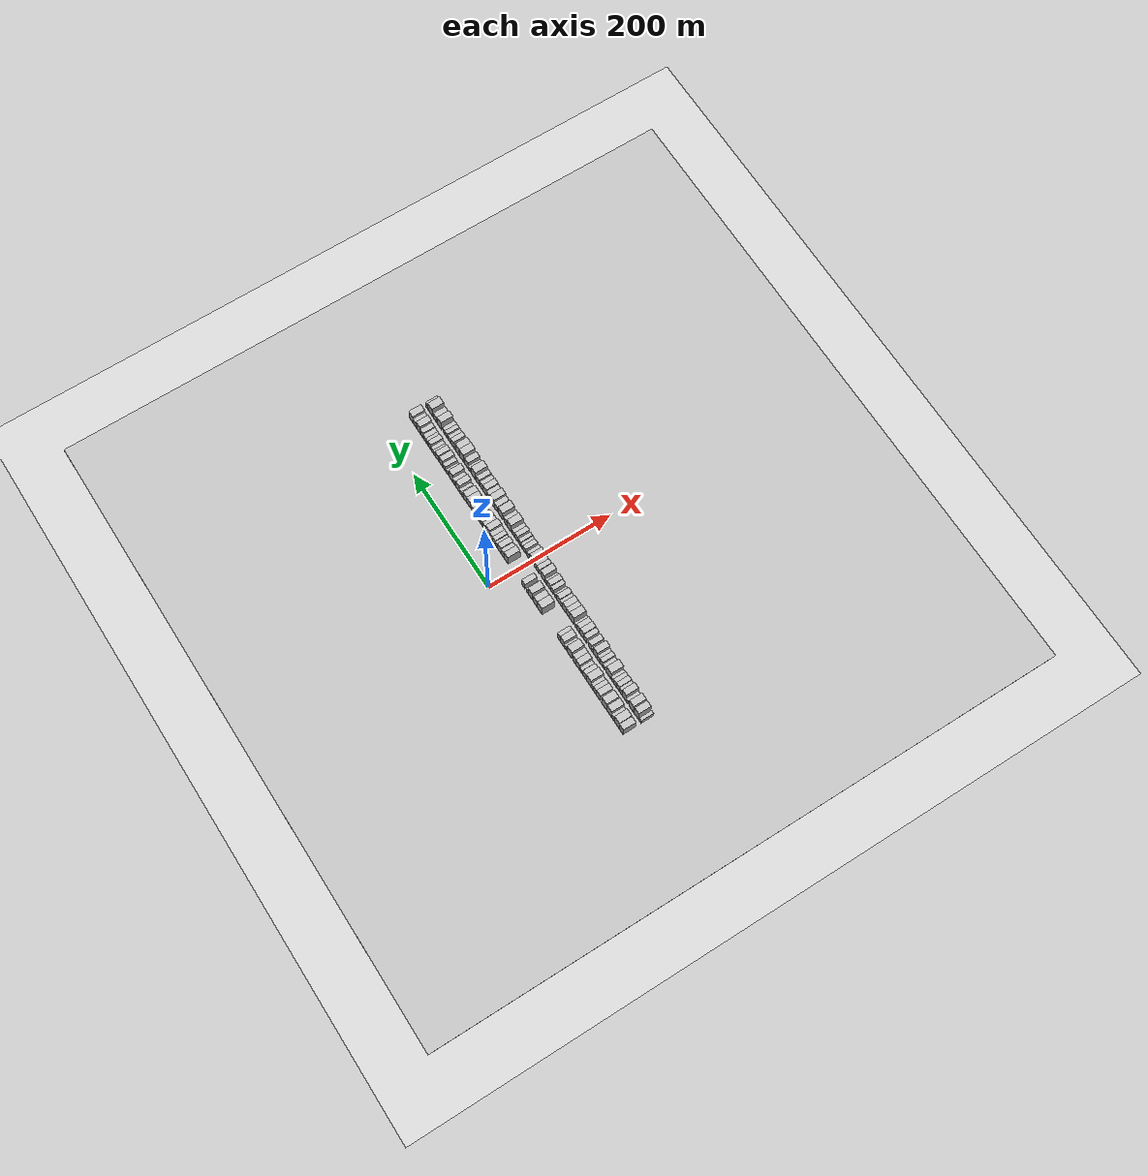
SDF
<?xml version="1.0" encoding="utf-8"?>

<sdf version="1.6">

   <world name="default">

      <gui fullscreen="0">

         <camera name="user_camera">

            <pose>-15 0 4.57585 0 0 0</pose>

            <view_controller>orbit</view_controller>

         </camera>

      </gui>

      <scene>

         <sky>

           <clouds>

             <speed>12</speed>

           </clouds>

         </sky>

         <ambient>0.4 0.4 0.4 1</ambient>

         <background>0.7 0.7 0.7 1</background>

         <shadows>1</shadows>

      </scene>

      <gravity>0 0 -9.8066</gravity>

      <magnetic_field>6e-06 2.3e-05 -4.2e-05</magnetic_field>

      <physics default="0" name="default_physics" type="ode">

         <ode>

            <solver>

               <type>quick</type>

               <iters>10</iters>

               <sor>1.0</sor>

               <use_dynamic_moi_rescaling>0</use_dynamic_moi_rescaling>

            </solver>

            <constraints>

               <cfm>0</cfm>

               <erp>0.2</erp>

               <contact_max_correcting_vel>100</contact_max_correcting_vel>

               <contact_surface_layer>0.001</contact_surface_layer>

            </constraints>

         </ode>

         <max_step_size>0.004</max_step_size>

         <real_time_factor>1</real_time_factor>

         <real_time_update_rate>250</real_time_update_rate>

      </physics>

      <light name="sun" type="directional">

         <cast_shadows>1</cast_shadows>

         <pose>0 0 10 0 0 0</pose>

         <diffuse>0.8 0.8 0.8 1</diffuse>

         <specular>0.2 0.2 0.2 1</specular>

         <attenuation>

            <range>1000</range>

            <constant>0.9</constant>

            <linear>0.01</linear>

            <quadratic>0.001</quadratic>

         </attenuation>

         <direction>-0.5 0.1 -0.9</direction>

      </light>

      <include>

         <name>ground_plane_1</name>

         <uri>model://HANNAS_ground_plane</uri>

         <pose>0 0 0  0 0 0</pose>

      </include>

      <include>

         <name>ground_plane_2</name>

         <uri>model://HANNAS_ground_plane</uri>

         <pose>100 0 0  0 0 0</pose>

      </include>

      <model name="building_1">

         <static>1</static>

         <pose frame="">50.0000 -272.9973 0 0.000000 0.000000 0.000000</pose>

         <link name="link">

            <pose frame="">0 0 10.50 0 0 0</pose>

            <collision name="collision">

               <geometry>

                  <box>

                     <size>20.0000 10.0054 21.0000</size>

                  </box>

               </geometry>

               <max_contacts>10</max_contacts>

               <surface>

                  <contact>

                     <ode/>

                  </contact>

                  <bounce/>

                  <friction>

                     <torsional>

                        <ode/>

                     </torsional>

                     <ode/>

                  </friction>

               </surface>

            </collision>

            <visual name="visual">

               <cast_shadows>0</cast_shadows>

               <geometry>

                  <box>

                     <size>20.0000 10.0054 21.0000</size>

                  </box>

               </geometry>

               <material>

                  <script>

                     <uri>model://HANNAS_wall/materials/scripts</uri>

                     <uri>model://HANNAS_wall/materials/textures</uri>

                     <name>vrc/HANNAS_wall</name>

                  </script>

               </material>

            </visual>

            <self_collide>0</self_collide>

            <enable_wind>0</enable_wind>

            <kinematic>0</kinematic>

         </link>

      </model>

      <model name="building_2">

         <static>1</static>

         <pose frame="">50.0000 -262.0783 0 0.000000 0.000000 0.000000</pose>

         <link name="link">

            <pose frame="">0 0 12.00 0 0 0</pose>

            <collision name="collision">

               <geometry>

                  <box>

                     <size>20.0000 11.8327 24.0000</size>

                  </box>

               </geometry>

               <max_contacts>10</max_contacts>

               <surface>

                  <contact>

                     <ode/>

                  </contact>

                  <bounce/>

                  <friction>

                     <torsional>

                        <ode/>

                     </torsional>

                     <ode/>

                  </friction>

               </surface>

            </collision>

            <visual name="visual">

               <cast_shadows>0</cast_shadows>

               <geometry>

                  <box>

                     <size>20.0000 11.8327 24.0000</size>

                  </box>

               </geometry>

               <material>

                  <script>

                     <uri>model://HANNAS_wall/materials/scripts</uri>

                     <uri>model://HANNAS_wall/materials/textures</uri>

                     <name>vrc/HANNAS_wall</name>

                  </script>

               </material>

            </visual>

            <self_collide>0</self_collide>

            <enable_wind>0</enable_wind>

            <kinematic>0</kinematic>

         </link>

      </model>

      <model name="building_3">

         <static>1</static>

         <pose frame="">50.0000 -252.6162 0 0.000000 0.000000 0.000000</pose>

         <link name="link">

            <pose frame="">0 0 7.50 0 0 0</pose>

            <collision name="collision">

               <geometry>

                  <box>

                     <size>20.0000 7.0915 15.0000</size>

                  </box>

               </geometry>

               <max_contacts>10</max_contacts>

               <surface>

                  <contact>

                     <ode/>

                  </contact>

                  <bounce/>

                  <friction>

                     <torsional>

                        <ode/>

                     </torsional>

                     <ode/>

                  </friction>

               </surface>

            </collision>

            <visual name="visual">

               <cast_shadows>0</cast_shadows>

               <geometry>

                  <box>

                     <size>20.0000 7.0915 15.0000</size>

                  </box>

               </geometry>

               <material>

                  <script>

                     <uri>model://HANNAS_wall/materials/scripts</uri>

                     <uri>model://HANNAS_wall/materials/textures</uri>

                     <name>vrc/HANNAS_wall</name>

                  </script>

               </material>

            </visual>

            <self_collide>0</self_collide>

            <enable_wind>0</enable_wind>

            <kinematic>0</kinematic>

         </link>

      </model>

      <model name="building_4">

         <static>1</static>

         <pose frame="">50.0000 -243.7639 0 0.000000 0.000000 0.000000</pose>

         <link name="link">

            <pose frame="">0 0 12.00 0 0 0</pose>

            <collision name="collision">

               <geometry>

                  <box>

                     <size>20.0000 10.6131 24.0000</size>

                  </box>

               </geometry>

               <max_contacts>10</max_contacts>

               <surface>

                  <contact>

                     <ode/>

                  </contact>

                  <bounce/>

                  <friction>

                     <torsional>

                        <ode/>

                     </torsional>

                     <ode/>

                  </friction>

               </surface>

            </collision>

            <visual name="visual">

               <cast_shadows>0</cast_shadows>

               <geometry>

                  <box>

                     <size>20.0000 10.6131 24.0000</size>

                  </box>

               </geometry>

               <material>

                  <script>

                     <uri>model://HANNAS_wall/materials/scripts</uri>

                     <uri>model://HANNAS_wall/materials/textures</uri>

                     <name>vrc/HANNAS_wall</name>

                  </script>

               </material>

            </visual>

            <self_collide>0</self_collide>

            <enable_wind>0</enable_wind>

            <kinematic>0</kinematic>

         </link>

      </model>

      <model name="building_5">

         <static>1</static>

         <pose frame="">50.0000 -230.4985 0 0.000000 0.000000 0.000000</pose>

         <link name="link">

            <pose frame="">0 0 12.00 0 0 0</pose>

            <collision name="collision">

               <geometry>

                  <box>

                     <size>20.0000 11.9177 24.0000</size>

                  </box>

               </geometry>

               <max_contacts>10</max_contacts>

               <surface>

                  <contact>

                     <ode/>

                  </contact>

                  <bounce/>

                  <friction>

                     <torsional>

                        <ode/>

                     </torsional>

                     <ode/>

                  </friction>

               </surface>

            </collision>

            <visual name="visual">

               <cast_shadows>0</cast_shadows>

               <geometry>

                  <box>

                     <size>20.0000 11.9177 24.0000</size>

                  </box>

               </geometry>

               <material>

                  <script>

                     <uri>model://HANNAS_wall/materials/scripts</uri>

                     <uri>model://HANNAS_wall/materials/textures</uri>

                     <name>vrc/HANNAS_wall</name>

                  </script>

               </material>

            </visual>

            <self_collide>0</self_collide>

            <enable_wind>0</enable_wind>

            <kinematic>0</kinematic>

         </link>

      </model>

      <model name="building_6">

         <static>1</static>

         <pose frame="">50.0000 -216.6666 0 0.000000 0.000000 0.000000</pose>

         <link name="link">

            <pose frame="">0 0 10.50 0 0 0</pose>

            <collision name="collision">

               <geometry>

                  <box>

                     <size>20.0000 9.7462 21.0000</size>

                  </box>

               </geometry>

               <max_contacts>10</max_contacts>

               <surface>

                  <contact>

                     <ode/>

                  </contact>

                  <bounce/>

                  <friction>

                     <torsional>

                        <ode/>

                     </torsional>

                     <ode/>

                  </friction>

               </surface>

            </collision>

            <visual name="visual">

               <cast_shadows>0</cast_shadows>

               <geometry>

                  <box>

                     <size>20.0000 9.7462 21.0000</size>

                  </box>

               </geometry>

               <material>

                  <script>

                     <uri>model://HANNAS_wall/materials/scripts</uri>

                     <uri>model://HANNAS_wall/materials/textures</uri>

                     <name>vrc/HANNAS_wall</name>

                  </script>

               </material>

            </visual>

            <self_collide>0</self_collide>

            <enable_wind>0</enable_wind>

            <kinematic>0</kinematic>

         </link>

      </model>

      <model name="building_7">

         <static>1</static>

         <pose frame="">50.0000 -208.0286 0 0.000000 0.000000 0.000000</pose>

         <link name="link">

            <pose frame="">0 0 9.00 0 0 0</pose>

            <collision name="collision">

               <geometry>

                  <box>

                     <size>20.0000 7.5296 18.0000</size>

                  </box>

               </geometry>

               <max_contacts>10</max_contacts>

               <surface>

                  <contact>

                     <ode/>

                  </contact>

                  <bounce/>

                  <friction>

                     <torsional>

                        <ode/>

                     </torsional>

                     <ode/>

                  </friction>

               </surface>

            </collision>

            <visual name="visual">

               <cast_shadows>0</cast_shadows>

               <geometry>

                  <box>

                     <size>20.0000 7.5296 18.0000</size>

                  </box>

               </geometry>

               <material>

                  <script>

                     <uri>model://HANNAS_wall/materials/scripts</uri>

                     <uri>model://HANNAS_wall/materials/textures</uri>

                     <name>vrc/HANNAS_wall</name>

                  </script>

               </material>

            </visual>

            <self_collide>0</self_collide>

            <enable_wind>0</enable_wind>

            <kinematic>0</kinematic>

         </link>

      </model>

      <model name="building_8">

         <static>1</static>

         <pose frame="">50.0000 -201.1453 0 0.000000 0.000000 0.000000</pose>

         <link name="link">

            <pose frame="">0 0 7.50 0 0 0</pose>

            <collision name="collision">

               <geometry>

                  <box>

                     <size>20.0000 6.2371 15.0000</size>

                  </box>

               </geometry>

               <max_contacts>10</max_contacts>

               <surface>

                  <contact>

                     <ode/>

                  </contact>

                  <bounce/>

                  <friction>

                     <torsional>

                        <ode/>

                     </torsional>

                     <ode/>

                  </friction>

               </surface>

            </collision>

            <visual name="visual">

               <cast_shadows>0</cast_shadows>

               <geometry>

                  <box>

                     <size>20.0000 6.2371 15.0000</size>

                  </box>

               </geometry>

               <material>

                  <script>

                     <uri>model://HANNAS_wall/materials/scripts</uri>

                     <uri>model://HANNAS_wall/materials/textures</uri>

                     <name>vrc/HANNAS_wall</name>

                  </script>

               </material>

            </visual>

            <self_collide>0</self_collide>

            <enable_wind>0</enable_wind>

            <kinematic>0</kinematic>

         </link>

      </model>

      <model name="building_9">

         <static>1</static>

         <pose frame="">50.0000 -192.2525 0 0.000000 0.000000 0.000000</pose>

         <link name="link">

            <pose frame="">0 0 12.00 0 0 0</pose>

            <collision name="collision">

               <geometry>

                  <box>

                     <size>20.0000 11.5486 24.0000</size>

                  </box>

               </geometry>

               <max_contacts>10</max_contacts>

               <surface>

                  <contact>

                     <ode/>

                  </contact>

                  <bounce/>

                  <friction>

                     <torsional>

                        <ode/>

                     </torsional>

                     <ode/>

                  </friction>

               </surface>

            </collision>

            <visual name="visual">

               <cast_shadows>0</cast_shadows>

               <geometry>

                  <box>

                     <size>20.0000 11.5486 24.0000</size>

                  </box>

               </geometry>

               <material>

                  <script>

                     <uri>model://HANNAS_wall/materials/scripts</uri>

                     <uri>model://HANNAS_wall/materials/textures</uri>

                     <name>vrc/HANNAS_wall</name>

                  </script>

               </material>

            </visual>

            <self_collide>0</self_collide>

            <enable_wind>0</enable_wind>

            <kinematic>0</kinematic>

         </link>

      </model>

      <model name="building_10">

         <static>1</static>

         <pose frame="">50.0000 -182.0756 0 0.000000 0.000000 0.000000</pose>

         <link name="link">

            <pose frame="">0 0 9.00 0 0 0</pose>

            <collision name="collision">

               <geometry>

                  <box>

                     <size>20.0000 8.8052 18.0000</size>

                  </box>

               </geometry>

               <max_contacts>10</max_contacts>

               <surface>

                  <contact>

                     <ode/>

                  </contact>

                  <bounce/>

                  <friction>

                     <torsional>

                        <ode/>

                     </torsional>

                     <ode/>

                  </friction>

               </surface>

            </collision>

            <visual name="visual">

               <cast_shadows>0</cast_shadows>

               <geometry>

                  <box>

                     <size>20.0000 8.8052 18.0000</size>

                  </box>

               </geometry>

               <material>

                  <script>

                     <uri>model://HANNAS_wall/materials/scripts</uri>

                     <uri>model://HANNAS_wall/materials/textures</uri>

                     <name>vrc/HANNAS_wall</name>

                  </script>

               </material>

            </visual>

            <self_collide>0</self_collide>

            <enable_wind>0</enable_wind>

            <kinematic>0</kinematic>

         </link>

      </model>

      <model name="building_11">

         <static>1</static>

         <pose frame="">50.0000 -172.8159 0 0.000000 0.000000 0.000000</pose>

         <link name="link">

            <pose frame="">0 0 6.00 0 0 0</pose>

            <collision name="collision">

               <geometry>

                  <box>

                     <size>20.0000 5.7141 12.0000</size>

                  </box>

               </geometry>

               <max_contacts>10</max_contacts>

               <surface>

                  <contact>

                     <ode/>

                  </contact>

                  <bounce/>

                  <friction>

                     <torsional>

                        <ode/>

                     </torsional>

                     <ode/>

                  </friction>

               </surface>

            </collision>

            <visual name="visual">

               <cast_shadows>0</cast_shadows>

               <geometry>

                  <box>

                     <size>20.0000 5.7141 12.0000</size>

                  </box>

               </geometry>

               <material>

                  <script>

                     <uri>model://HANNAS_wall/materials/scripts</uri>

                     <uri>model://HANNAS_wall/materials/textures</uri>

                     <name>vrc/HANNAS_wall</name>

                  </script>

               </material>

            </visual>

            <self_collide>0</self_collide>

            <enable_wind>0</enable_wind>

            <kinematic>0</kinematic>

         </link>

      </model>

      <model name="building_12">

         <static>1</static>

         <pose frame="">50.0000 -165.0856 0 0.000000 0.000000 0.000000</pose>

         <link name="link">

            <pose frame="">0 0 10.50 0 0 0</pose>

            <collision name="collision">

               <geometry>

                  <box>

                     <size>20.0000 9.7466 21.0000</size>

                  </box>

               </geometry>

               <max_contacts>10</max_contacts>

               <surface>

                  <contact>

                     <ode/>

                  </contact>

                  <bounce/>

                  <friction>

                     <torsional>

                        <ode/>

                     </torsional>

                     <ode/>

                  </friction>

               </surface>

            </collision>

            <visual name="visual">

               <cast_shadows>0</cast_shadows>

               <geometry>

                  <box>

                     <size>20.0000 9.7466 21.0000</size>

                  </box>

               </geometry>

               <material>

                  <script>

                     <uri>model://HANNAS_wall/materials/scripts</uri>

                     <uri>model://HANNAS_wall/materials/textures</uri>

                     <name>vrc/HANNAS_wall</name>

                  </script>

               </material>

            </visual>

            <self_collide>0</self_collide>

            <enable_wind>0</enable_wind>

            <kinematic>0</kinematic>

         </link>

      </model>

      <model name="building_13">

         <static>1</static>

         <pose frame="">50.0000 -156.0007 0 0.000000 0.000000 0.000000</pose>

         <link name="link">

            <pose frame="">0 0 10.50 0 0 0</pose>

            <collision name="collision">

               <geometry>

                  <box>

                     <size>20.0000 8.4233 21.0000</size>

                  </box>

               </geometry>

               <max_contacts>10</max_contacts>

               <surface>

                  <contact>

                     <ode/>

                  </contact>

                  <bounce/>

                  <friction>

                     <torsional>

                        <ode/>

                     </torsional>

                     <ode/>

                  </friction>

               </surface>

            </collision>

            <visual name="visual">

               <cast_shadows>0</cast_shadows>

               <geometry>

                  <box>

                     <size>20.0000 8.4233 21.0000</size>

                  </box>

               </geometry>

               <material>

                  <script>

                     <uri>model://HANNAS_wall/materials/scripts</uri>

                     <uri>model://HANNAS_wall/materials/textures</uri>

                     <name>vrc/HANNAS_wall</name>

                  </script>

               </material>

            </visual>

            <self_collide>0</self_collide>

            <enable_wind>0</enable_wind>

            <kinematic>0</kinematic>

         </link>

      </model>

      <model name="building_14">

         <static>1</static>

         <pose frame="">50.0000 -143.8482 0 0.000000 0.000000 0.000000</pose>

         <link name="link">

            <pose frame="">0 0 12.00 0 0 0</pose>

            <collision name="collision">

               <geometry>

                  <box>

                     <size>20.0000 11.8817 24.0000</size>

                  </box>

               </geometry>

               <max_contacts>10</max_contacts>

               <surface>

                  <contact>

                     <ode/>

                  </contact>

                  <bounce/>

                  <friction>

                     <torsional>

                        <ode/>

                     </torsional>

                     <ode/>

                  </friction>

               </surface>

            </collision>

            <visual name="visual">

               <cast_shadows>0</cast_shadows>

               <geometry>

                  <box>

                     <size>20.0000 11.8817 24.0000</size>

                  </box>

               </geometry>

               <material>

                  <script>

                     <uri>model://HANNAS_wall/materials/scripts</uri>

                     <uri>model://HANNAS_wall/materials/textures</uri>

                     <name>vrc/HANNAS_wall</name>

                  </script>

               </material>

            </visual>

            <self_collide>0</self_collide>

            <enable_wind>0</enable_wind>

            <kinematic>0</kinematic>

         </link>

      </model>

      <model name="building_15">

         <static>1</static>

         <pose frame="">50.0000 -133.4855 0 0.000000 0.000000 0.000000</pose>

         <link name="link">

            <pose frame="">0 0 6.00 0 0 0</pose>

            <collision name="collision">

               <geometry>

                  <box>

                     <size>20.0000 4.8438 12.0000</size>

                  </box>

               </geometry>

               <max_contacts>10</max_contacts>

               <surface>

                  <contact>

                     <ode/>

                  </contact>

                  <bounce/>

                  <friction>

                     <torsional>

                        <ode/>

                     </torsional>

                     <ode/>

                  </friction>

               </surface>

            </collision>

            <visual name="visual">

               <cast_shadows>0</cast_shadows>

               <geometry>

                  <box>

                     <size>20.0000 4.8438 12.0000</size>

                  </box>

               </geometry>

               <material>

                  <script>

                     <uri>model://HANNAS_wall/materials/scripts</uri>

                     <uri>model://HANNAS_wall/materials/textures</uri>

                     <name>vrc/HANNAS_wall</name>

                  </script>

               </material>

            </visual>

            <self_collide>0</self_collide>

            <enable_wind>0</enable_wind>

            <kinematic>0</kinematic>

         </link>

      </model>

      <model name="building_16">

         <static>1</static>

         <pose frame="">50.0000 -125.9108 0 0.000000 0.000000 0.000000</pose>

         <link name="link">

            <pose frame="">0 0 10.50 0 0 0</pose>

            <collision name="collision">

               <geometry>

                  <box>

                     <size>20.0000 10.3055 21.0000</size>

                  </box>

               </geometry>

               <max_contacts>10</max_contacts>

               <surface>

                  <contact>

                     <ode/>

                  </contact>

                  <bounce/>

                  <friction>

                     <torsional>

                        <ode/>

                     </torsional>

                     <ode/>

                  </friction>

               </surface>

            </collision>

            <visual name="visual">

               <cast_shadows>0</cast_shadows>

               <geometry>

                  <box>

                     <size>20.0000 10.3055 21.0000</size>

                  </box>

               </geometry>

               <material>

                  <script>

                     <uri>model://HANNAS_wall/materials/scripts</uri>

                     <uri>model://HANNAS_wall/materials/textures</uri>

                     <name>vrc/HANNAS_wall</name>

                  </script>

               </material>

            </visual>

            <self_collide>0</self_collide>

            <enable_wind>0</enable_wind>

            <kinematic>0</kinematic>

         </link>

      </model>

      <model name="building_17">

         <static>1</static>

         <pose frame="">50.0000 -117.1440 0 0.000000 0.000000 0.000000</pose>

         <link name="link">

            <pose frame="">0 0 9.00 0 0 0</pose>

            <collision name="collision">

               <geometry>

                  <box>

                     <size>20.0000 7.2282 18.0000</size>

                  </box>

               </geometry>

               <max_contacts>10</max_contacts>

               <surface>

                  <contact>

                     <ode/>

                  </contact>

                  <bounce/>

                  <friction>

                     <torsional>

                        <ode/>

                     </torsional>

                     <ode/>

                  </friction>

               </surface>

            </collision>

            <visual name="visual">

               <cast_shadows>0</cast_shadows>

               <geometry>

                  <box>

                     <size>20.0000 7.2282 18.0000</size>

                  </box>

               </geometry>

               <material>

                  <script>

                     <uri>model://HANNAS_wall/materials/scripts</uri>

                     <uri>model://HANNAS_wall/materials/textures</uri>

                     <name>vrc/HANNAS_wall</name>

                  </script>

               </material>

            </visual>

            <self_collide>0</self_collide>

            <enable_wind>0</enable_wind>

            <kinematic>0</kinematic>

         </link>

      </model>

      <model name="building_18">

         <static>1</static>

         <pose frame="">50.0000 -68.6288 0 0.000000 0.000000 0.000000</pose>

         <link name="link">

            <pose frame="">0 0 12.00 0 0 0</pose>

            <collision name="collision">

               <geometry>

                  <box>

                     <size>20.0000 11.9341 24.0000</size>

                  </box>

               </geometry>

               <max_contacts>10</max_contacts>

               <surface>

                  <contact>

                     <ode/>

                  </contact>

                  <bounce/>

                  <friction>

                     <torsional>

                        <ode/>

                     </torsional>

                     <ode/>

                  </friction>

               </surface>

            </collision>

            <visual name="visual">

               <cast_shadows>0</cast_shadows>

               <geometry>

                  <box>

                     <size>20.0000 11.9341 24.0000</size>

                  </box>

               </geometry>

               <material>

                  <script>

                     <uri>model://HANNAS_wall/materials/scripts</uri>

                     <uri>model://HANNAS_wall/materials/textures</uri>

                     <name>vrc/HANNAS_wall</name>

                  </script>

               </material>

            </visual>

            <self_collide>0</self_collide>

            <enable_wind>0</enable_wind>

            <kinematic>0</kinematic>

         </link>

      </model>

      <model name="building_19">

         <static>1</static>

         <pose frame="">50.0000 -57.4570 0 0.000000 0.000000 0.000000</pose>

         <link name="link">

            <pose frame="">0 0 10.50 0 0 0</pose>

            <collision name="collision">

               <geometry>

                  <box>

                     <size>20.0000 10.4093 21.0000</size>

                  </box>

               </geometry>

               <max_contacts>10</max_contacts>

               <surface>

                  <contact>

                     <ode/>

                  </contact>

                  <bounce/>

                  <friction>

                     <torsional>

                        <ode/>

                     </torsional>

                     <ode/>

                  </friction>

               </surface>

            </collision>

            <visual name="visual">

               <cast_shadows>0</cast_shadows>

               <geometry>

                  <box>

                     <size>20.0000 10.4093 21.0000</size>

                  </box>

               </geometry>

               <material>

                  <script>

                     <uri>model://HANNAS_wall/materials/scripts</uri>

                     <uri>model://HANNAS_wall/materials/textures</uri>

                     <name>vrc/HANNAS_wall</name>

                  </script>

               </material>

            </visual>

            <self_collide>0</self_collide>

            <enable_wind>0</enable_wind>

            <kinematic>0</kinematic>

         </link>

      </model>

      <model name="building_20">

         <static>1</static>

         <pose frame="">50.0000 -43.7756 0 0.000000 0.000000 0.000000</pose>

         <link name="link">

            <pose frame="">0 0 12.00 0 0 0</pose>

            <collision name="collision">

               <geometry>

                  <box>

                     <size>20.0000 10.9534 24.0000</size>

                  </box>

               </geometry>

               <max_contacts>10</max_contacts>

               <surface>

                  <contact>

                     <ode/>

                  </contact>

                  <bounce/>

                  <friction>

                     <torsional>

                        <ode/>

                     </torsional>

                     <ode/>

                  </friction>

               </surface>

            </collision>

            <visual name="visual">

               <cast_shadows>0</cast_shadows>

               <geometry>

                  <box>

                     <size>20.0000 10.9534 24.0000</size>

                  </box>

               </geometry>

               <material>

                  <script>

                     <uri>model://HANNAS_wall/materials/scripts</uri>

                     <uri>model://HANNAS_wall/materials/textures</uri>

                     <name>vrc/HANNAS_wall</name>

                  </script>

               </material>

            </visual>

            <self_collide>0</self_collide>

            <enable_wind>0</enable_wind>

            <kinematic>0</kinematic>

         </link>

      </model>

      <model name="building_21">

         <static>1</static>

         <pose frame="">50.0000 -35.7943 0 0.000000 0.000000 0.000000</pose>

         <link name="link">

            <pose frame="">0 0 6.00 0 0 0</pose>

            <collision name="collision">

               <geometry>

                  <box>

                     <size>20.0000 5.0093 12.0000</size>

                  </box>

               </geometry>

               <max_contacts>10</max_contacts>

               <surface>

                  <contact>

                     <ode/>

                  </contact>

                  <bounce/>

                  <friction>

                     <torsional>

                        <ode/>

                     </torsional>

                     <ode/>

                  </friction>

               </surface>

            </collision>

            <visual name="visual">

               <cast_shadows>0</cast_shadows>

               <geometry>

                  <box>

                     <size>20.0000 5.0093 12.0000</size>

                  </box>

               </geometry>

               <material>

                  <script>

                     <uri>model://HANNAS_wall/materials/scripts</uri>

                     <uri>model://HANNAS_wall/materials/textures</uri>

                     <name>vrc/HANNAS_wall</name>

                  </script>

               </material>

            </visual>

            <self_collide>0</self_collide>

            <enable_wind>0</enable_wind>

            <kinematic>0</kinematic>

         </link>

      </model>

      <model name="building_22">

         <static>1</static>

         <pose frame="">50.0000 -26.0420 0 0.000000 0.000000 0.000000</pose>

         <link name="link">

            <pose frame="">0 0 9.00 0 0 0</pose>

            <collision name="collision">

               <geometry>

                  <box>

                     <size>20.0000 8.4953 18.0000</size>

                  </box>

               </geometry>

               <max_contacts>10</max_contacts>

               <surface>

                  <contact>

                     <ode/>

                  </contact>

                  <bounce/>

                  <friction>

                     <torsional>

                        <ode/>

                     </torsional>

                     <ode/>

                  </friction>

               </surface>

            </collision>

            <visual name="visual">

               <cast_shadows>0</cast_shadows>

               <geometry>

                  <box>

                     <size>20.0000 8.4953 18.0000</size>

                  </box>

               </geometry>

               <material>

                  <script>

                     <uri>model://HANNAS_wall/materials/scripts</uri>

                     <uri>model://HANNAS_wall/materials/textures</uri>

                     <name>vrc/HANNAS_wall</name>

                  </script>

               </material>

            </visual>

            <self_collide>0</self_collide>

            <enable_wind>0</enable_wind>

            <kinematic>0</kinematic>

         </link>

      </model>

      <model name="building_23">

         <static>1</static>

         <pose frame="">50.0000 18.8368 0 0.000000 0.000000 0.000000</pose>

         <link name="link">

            <pose frame="">0 0 12.00 0 0 0</pose>

            <collision name="collision">

               <geometry>

                  <box>

                     <size>20.0000 9.7541 24.0000</size>

                  </box>

               </geometry>

               <max_contacts>10</max_contacts>

               <surface>

                  <contact>

                     <ode/>

                  </contact>

                  <bounce/>

                  <friction>

                     <torsional>

                        <ode/>

                     </torsional>

                     <ode/>

                  </friction>

               </surface>

            </collision>

            <visual name="visual">

               <cast_shadows>0</cast_shadows>

               <geometry>

                  <box>

                     <size>20.0000 9.7541 24.0000</size>

                  </box>

               </geometry>

               <material>

                  <script>

                     <uri>model://HANNAS_wall/materials/scripts</uri>

                     <uri>model://HANNAS_wall/materials/textures</uri>

                     <name>vrc/HANNAS_wall</name>

                  </script>

               </material>

            </visual>

            <self_collide>0</self_collide>

            <enable_wind>0</enable_wind>

            <kinematic>0</kinematic>

         </link>

      </model>

      <model name="building_24">

         <static>1</static>

         <pose frame="">50.0000 27.8491 0 0.000000 0.000000 0.000000</pose>

         <link name="link">

            <pose frame="">0 0 9.00 0 0 0</pose>

            <collision name="collision">

               <geometry>

                  <box>

                     <size>20.0000 8.2705 18.0000</size>

                  </box>

               </geometry>

               <max_contacts>10</max_contacts>

               <surface>

                  <contact>

                     <ode/>

                  </contact>

                  <bounce/>

                  <friction>

                     <torsional>

                        <ode/>

                     </torsional>

                     <ode/>

                  </friction>

               </surface>

            </collision>

            <visual name="visual">

               <cast_shadows>0</cast_shadows>

               <geometry>

                  <box>

                     <size>20.0000 8.2705 18.0000</size>

                  </box>

               </geometry>

               <material>

                  <script>

                     <uri>model://HANNAS_wall/materials/scripts</uri>

                     <uri>model://HANNAS_wall/materials/textures</uri>

                     <name>vrc/HANNAS_wall</name>

                  </script>

               </material>

            </visual>

            <self_collide>0</self_collide>

            <enable_wind>0</enable_wind>

            <kinematic>0</kinematic>

         </link>

      </model>

      <model name="building_25">

         <static>1</static>

         <pose frame="">50.0000 36.3773 0 0.000000 0.000000 0.000000</pose>

         <link name="link">

            <pose frame="">0 0 10.50 0 0 0</pose>

            <collision name="collision">

               <geometry>

                  <box>

                     <size>20.0000 8.7859 21.0000</size>

                  </box>

               </geometry>

               <max_contacts>10</max_contacts>

               <surface>

                  <contact>

                     <ode/>

                  </contact>

                  <bounce/>

                  <friction>

                     <torsional>

                        <ode/>

                     </torsional>

                     <ode/>

                  </friction>

               </surface>

            </collision>

            <visual name="visual">

               <cast_shadows>0</cast_shadows>

               <geometry>

                  <box>

                     <size>20.0000 8.7859 21.0000</size>

                  </box>

               </geometry>

               <material>

                  <script>

                     <uri>model://HANNAS_wall/materials/scripts</uri>

                     <uri>model://HANNAS_wall/materials/textures</uri>

                     <name>vrc/HANNAS_wall</name>

                  </script>

               </material>

            </visual>

            <self_collide>0</self_collide>

            <enable_wind>0</enable_wind>

            <kinematic>0</kinematic>

         </link>

      </model>

      <model name="building_26">

         <static>1</static>

         <pose frame="">50.0000 43.7820 0 0.000000 0.000000 0.000000</pose>

         <link name="link">

            <pose frame="">0 0 7.50 0 0 0</pose>

            <collision name="collision">

               <geometry>

                  <box>

                     <size>20.0000 6.0235 15.0000</size>

                  </box>

               </geometry>

               <max_contacts>10</max_contacts>

               <surface>

                  <contact>

                     <ode/>

                  </contact>

                  <bounce/>

                  <friction>

                     <torsional>

                        <ode/>

                     </torsional>

                     <ode/>

                  </friction>

               </surface>

            </collision>

            <visual name="visual">

               <cast_shadows>0</cast_shadows>

               <geometry>

                  <box>

                     <size>20.0000 6.0235 15.0000</size>

                  </box>

               </geometry>

               <material>

                  <script>

                     <uri>model://HANNAS_wall/materials/scripts</uri>

                     <uri>model://HANNAS_wall/materials/textures</uri>

                     <name>vrc/HANNAS_wall</name>

                  </script>

               </material>

            </visual>

            <self_collide>0</self_collide>

            <enable_wind>0</enable_wind>

            <kinematic>0</kinematic>

         </link>

      </model>

      <model name="building_27">

         <static>1</static>

         <pose frame="">50.0000 50.4874 0 0.000000 0.000000 0.000000</pose>

         <link name="link">

            <pose frame="">0 0 9.00 0 0 0</pose>

            <collision name="collision">

               <geometry>

                  <box>

                     <size>20.0000 7.3873 18.0000</size>

                  </box>

               </geometry>

               <max_contacts>10</max_contacts>

               <surface>

                  <contact>

                     <ode/>

                  </contact>

                  <bounce/>

                  <friction>

                     <torsional>

                        <ode/>

                     </torsional>

                     <ode/>

                  </friction>

               </surface>

            </collision>

            <visual name="visual">

               <cast_shadows>0</cast_shadows>

               <geometry>

                  <box>

                     <size>20.0000 7.3873 18.0000</size>

                  </box>

               </geometry>

               <material>

                  <script>

                     <uri>model://HANNAS_wall/materials/scripts</uri>

                     <uri>model://HANNAS_wall/materials/textures</uri>

                     <name>vrc/HANNAS_wall</name>

                  </script>

               </material>

            </visual>

            <self_collide>0</self_collide>

            <enable_wind>0</enable_wind>

            <kinematic>0</kinematic>

         </link>

      </model>

      <model name="building_28">

         <static>1</static>

         <pose frame="">50.0000 57.9974 0 0.000000 0.000000 0.000000</pose>

         <link name="link">

            <pose frame="">0 0 9.00 0 0 0</pose>

            <collision name="collision">

               <geometry>

                  <box>

                     <size>20.0000 7.6327 18.0000</size>

                  </box>

               </geometry>

               <max_contacts>10</max_contacts>

               <surface>

                  <contact>

                     <ode/>

                  </contact>

                  <bounce/>

                  <friction>

                     <torsional>

                        <ode/>

                     </torsional>

                     <ode/>

                  </friction>

               </surface>

            </collision>

            <visual name="visual">

               <cast_shadows>0</cast_shadows>

               <geometry>

                  <box>

                     <size>20.0000 7.6327 18.0000</size>

                  </box>

               </geometry>

               <material>

                  <script>

                     <uri>model://HANNAS_wall/materials/scripts</uri>

                     <uri>model://HANNAS_wall/materials/textures</uri>

                     <name>vrc/HANNAS_wall</name>

                  </script>

               </material>

            </visual>

            <self_collide>0</self_collide>

            <enable_wind>0</enable_wind>

            <kinematic>0</kinematic>

         </link>

      </model>

      <model name="building_29">

         <static>1</static>

         <pose frame="">50.0000 66.8015 0 0.000000 0.000000 0.000000</pose>

         <link name="link">

            <pose frame="">0 0 12.00 0 0 0</pose>

            <collision name="collision">

               <geometry>

                  <box>

                     <size>20.0000 9.9755 24.0000</size>

                  </box>

               </geometry>

               <max_contacts>10</max_contacts>

               <surface>

                  <contact>

                     <ode/>

                  </contact>

                  <bounce/>

                  <friction>

                     <torsional>

                        <ode/>

                     </torsional>

                     <ode/>

                  </friction>

               </surface>

            </collision>

            <visual name="visual">

               <cast_shadows>0</cast_shadows>

               <geometry>

                  <box>

                     <size>20.0000 9.9755 24.0000</size>

                  </box>

               </geometry>

               <material>

                  <script>

                     <uri>model://HANNAS_wall/materials/scripts</uri>

                     <uri>model://HANNAS_wall/materials/textures</uri>

                     <name>vrc/HANNAS_wall</name>

                  </script>

               </material>

            </visual>

            <self_collide>0</self_collide>

            <enable_wind>0</enable_wind>

            <kinematic>0</kinematic>

         </link>

      </model>

      <model name="building_30">

         <static>1</static>

         <pose frame="">50.0000 78.0534 0 0.000000 0.000000 0.000000</pose>

         <link name="link">

            <pose frame="">0 0 7.50 0 0 0</pose>

            <collision name="collision">

               <geometry>

                  <box>

                     <size>20.0000 6.5283 15.0000</size>

                  </box>

               </geometry>

               <max_contacts>10</max_contacts>

               <surface>

                  <contact>

                     <ode/>

                  </contact>

                  <bounce/>

                  <friction>

                     <torsional>

                        <ode/>

                     </torsional>

                     <ode/>

                  </friction>

               </surface>

            </collision>

            <visual name="visual">

               <cast_shadows>0</cast_shadows>

               <geometry>

                  <box>

                     <size>20.0000 6.5283 15.0000</size>

                  </box>

               </geometry>

               <material>

                  <script>

                     <uri>model://HANNAS_wall/materials/scripts</uri>

                     <uri>model://HANNAS_wall/materials/textures</uri>

                     <name>vrc/HANNAS_wall</name>

                  </script>

               </material>

            </visual>

            <self_collide>0</self_collide>

            <enable_wind>0</enable_wind>

            <kinematic>0</kinematic>

         </link>

      </model>

      <model name="building_31">

         <static>1</static>

         <pose frame="">50.0000 84.7035 0 0.000000 0.000000 0.000000</pose>

         <link name="link">

            <pose frame="">0 0 7.50 0 0 0</pose>

            <collision name="collision">

               <geometry>

                  <box>

                     <size>20.0000 6.7718 15.0000</size>

                  </box>

               </geometry>

               <max_contacts>10</max_contacts>

               <surface>

                  <contact>

                     <ode/>

                  </contact>

                  <bounce/>

                  <friction>

                     <torsional>

                        <ode/>

                     </torsional>

                     <ode/>

                  </friction>

               </surface>

            </collision>

            <visual name="visual">

               <cast_shadows>0</cast_shadows>

               <geometry>

                  <box>

                     <size>20.0000 6.7718 15.0000</size>

                  </box>

               </geometry>

               <material>

                  <script>

                     <uri>model://HANNAS_wall/materials/scripts</uri>

                     <uri>model://HANNAS_wall/materials/textures</uri>

                     <name>vrc/HANNAS_wall</name>

                  </script>

               </material>

            </visual>

            <self_collide>0</self_collide>

            <enable_wind>0</enable_wind>

            <kinematic>0</kinematic>

         </link>

      </model>

      <model name="building_32">

         <static>1</static>

         <pose frame="">50.0000 90.9740 0 0.000000 0.000000 0.000000</pose>

         <link name="link">

            <pose frame="">0 0 6.00 0 0 0</pose>

            <collision name="collision">

               <geometry>

                  <box>

                     <size>20.0000 5.7691 12.0000</size>

                  </box>

               </geometry>

               <max_contacts>10</max_contacts>

               <surface>

                  <contact>

                     <ode/>

                  </contact>

                  <bounce/>

                  <friction>

                     <torsional>

                        <ode/>

                     </torsional>

                     <ode/>

                  </friction>

               </surface>

            </collision>

            <visual name="visual">

               <cast_shadows>0</cast_shadows>

               <geometry>

                  <box>

                     <size>20.0000 5.7691 12.0000</size>

                  </box>

               </geometry>

               <material>

                  <script>

                     <uri>model://HANNAS_wall/materials/scripts</uri>

                     <uri>model://HANNAS_wall/materials/textures</uri>

                     <name>vrc/HANNAS_wall</name>

                  </script>

               </material>

            </visual>

            <self_collide>0</self_collide>

            <enable_wind>0</enable_wind>

            <kinematic>0</kinematic>

         </link>

      </model>

      <model name="building_33">

         <static>1</static>

         <pose frame="">50.0000 100.4630 0 0.000000 0.000000 0.000000</pose>

         <link name="link">

            <pose frame="">0 0 7.50 0 0 0</pose>

            <collision name="collision">

               <geometry>

                  <box>

                     <size>20.0000 7.2090 15.0000</size>

                  </box>

               </geometry>

               <max_contacts>10</max_contacts>

               <surface>

                  <contact>

                     <ode/>

                  </contact>

                  <bounce/>

                  <friction>

                     <torsional>

                        <ode/>

                     </torsional>

                     <ode/>

                  </friction>

               </surface>

            </collision>

            <visual name="visual">

               <cast_shadows>0</cast_shadows>

               <geometry>

                  <box>

                     <size>20.0000 7.2090 15.0000</size>

                  </box>

               </geometry>

               <material>

                  <script>

                     <uri>model://HANNAS_wall/materials/scripts</uri>

                     <uri>model://HANNAS_wall/materials/textures</uri>

                     <name>vrc/HANNAS_wall</name>

                  </script>

               </material>

            </visual>

            <self_collide>0</self_collide>

            <enable_wind>0</enable_wind>

            <kinematic>0</kinematic>

         </link>

      </model>

      <model name="building_34">

         <static>1</static>

         <pose frame="">50.0000 109.0796 0 0.000000 0.000000 0.000000</pose>

         <link name="link">

            <pose frame="">0 0 7.50 0 0 0</pose>

            <collision name="collision">

               <geometry>

                  <box>

                     <size>20.0000 6.0240 15.0000</size>

                  </box>

               </geometry>

               <max_contacts>10</max_contacts>

               <surface>

                  <contact>

                     <ode/>

                  </contact>

                  <bounce/>

                  <friction>

                     <torsional>

                        <ode/>

                     </torsional>

                     <ode/>

                  </friction>

               </surface>

            </collision>

            <visual name="visual">

               <cast_shadows>0</cast_shadows>

               <geometry>

                  <box>

                     <size>20.0000 6.0240 15.0000</size>

                  </box>

               </geometry>

               <material>

                  <script>

                     <uri>model://HANNAS_wall/materials/scripts</uri>

                     <uri>model://HANNAS_wall/materials/textures</uri>

                     <name>vrc/HANNAS_wall</name>

                  </script>

               </material>

            </visual>

            <self_collide>0</self_collide>

            <enable_wind>0</enable_wind>

            <kinematic>0</kinematic>

         </link>

      </model>

      <model name="building_35">

         <static>1</static>

         <pose frame="">50.0000 118.5853 0 0.000000 0.000000 0.000000</pose>

         <link name="link">

            <pose frame="">0 0 10.50 0 0 0</pose>

            <collision name="collision">

               <geometry>

                  <box>

                     <size>20.0000 8.9874 21.0000</size>

                  </box>

               </geometry>

               <max_contacts>10</max_contacts>

               <surface>

                  <contact>

                     <ode/>

                  </contact>

                  <bounce/>

                  <friction>

                     <torsional>

                        <ode/>

                     </torsional>

                     <ode/>

                  </friction>

               </surface>

            </collision>

            <visual name="visual">

               <cast_shadows>0</cast_shadows>

               <geometry>

                  <box>

                     <size>20.0000 8.9874 21.0000</size>

                  </box>

               </geometry>

               <material>

                  <script>

                     <uri>model://HANNAS_wall/materials/scripts</uri>

                     <uri>model://HANNAS_wall/materials/textures</uri>

                     <name>vrc/HANNAS_wall</name>

                  </script>

               </material>

            </visual>

            <self_collide>0</self_collide>

            <enable_wind>0</enable_wind>

            <kinematic>0</kinematic>

         </link>

      </model>

      <model name="building_36">

         <static>1</static>

         <pose frame="">50.0000 127.9263 0 0.000000 0.000000 0.000000</pose>

         <link name="link">

            <pose frame="">0 0 10.50 0 0 0</pose>

            <collision name="collision">

               <geometry>

                  <box>

                     <size>20.0000 9.6948 21.0000</size>

                  </box>

               </geometry>

               <max_contacts>10</max_contacts>

               <surface>

                  <contact>

                     <ode/>

                  </contact>

                  <bounce/>

                  <friction>

                     <torsional>

                        <ode/>

                     </torsional>

                     <ode/>

                  </friction>

               </surface>

            </collision>

            <visual name="visual">

               <cast_shadows>0</cast_shadows>

               <geometry>

                  <box>

                     <size>20.0000 9.6948 21.0000</size>

                  </box>

               </geometry>

               <material>

                  <script>

                     <uri>model://HANNAS_wall/materials/scripts</uri>

                     <uri>model://HANNAS_wall/materials/textures</uri>

                     <name>vrc/HANNAS_wall</name>

                  </script>

               </material>

            </visual>

            <self_collide>0</self_collide>

            <enable_wind>0</enable_wind>

            <kinematic>0</kinematic>

         </link>

      </model>

      <model name="building_37">

         <static>1</static>

         <pose frame="">50.0000 135.3157 0 0.000000 0.000000 0.000000</pose>

         <link name="link">

            <pose frame="">0 0 6.00 0 0 0</pose>

            <collision name="collision">

               <geometry>

                  <box>

                     <size>20.0000 5.0840 12.0000</size>

                  </box>

               </geometry>

               <max_contacts>10</max_contacts>

               <surface>

                  <contact>

                     <ode/>

                  </contact>

                  <bounce/>

                  <friction>

                     <torsional>

                        <ode/>

                     </torsional>

                     <ode/>

                  </friction>

               </surface>

            </collision>

            <visual name="visual">

               <cast_shadows>0</cast_shadows>

               <geometry>

                  <box>

                     <size>20.0000 5.0840 12.0000</size>

                  </box>

               </geometry>

               <material>

                  <script>

                     <uri>model://HANNAS_wall/materials/scripts</uri>

                     <uri>model://HANNAS_wall/materials/textures</uri>

                     <name>vrc/HANNAS_wall</name>

                  </script>

               </material>

            </visual>

            <self_collide>0</self_collide>

            <enable_wind>0</enable_wind>

            <kinematic>0</kinematic>

         </link>

      </model>

      <model name="building_38">

         <static>1</static>

         <pose frame="">50.0000 140.4086 0 0.000000 0.000000 0.000000</pose>

         <link name="link">

            <pose frame="">0 0 6.00 0 0 0</pose>

            <collision name="collision">

               <geometry>

                  <box>

                     <size>20.0000 5.1019 12.0000</size>

                  </box>

               </geometry>

               <max_contacts>10</max_contacts>

               <surface>

                  <contact>

                     <ode/>

                  </contact>

                  <bounce/>

                  <friction>

                     <torsional>

                        <ode/>

                     </torsional>

                     <ode/>

                  </friction>

               </surface>

            </collision>

            <visual name="visual">

               <cast_shadows>0</cast_shadows>

               <geometry>

                  <box>

                     <size>20.0000 5.1019 12.0000</size>

                  </box>

               </geometry>

               <material>

                  <script>

                     <uri>model://HANNAS_wall/materials/scripts</uri>

                     <uri>model://HANNAS_wall/materials/textures</uri>

                     <name>vrc/HANNAS_wall</name>

                  </script>

               </material>

            </visual>

            <self_collide>0</self_collide>

            <enable_wind>0</enable_wind>

            <kinematic>0</kinematic>

         </link>

      </model>

      <model name="building_39">

         <static>1</static>

         <pose frame="">50.0000 147.6372 0 0.000000 0.000000 0.000000</pose>

         <link name="link">

            <pose frame="">0 0 10.50 0 0 0</pose>

            <collision name="collision">

               <geometry>

                  <box>

                     <size>20.0000 9.3553 21.0000</size>

                  </box>

               </geometry>

               <max_contacts>10</max_contacts>

               <surface>

                  <contact>

                     <ode/>

                  </contact>

                  <bounce/>

                  <friction>

                     <torsional>

                        <ode/>

                     </torsional>

                     <ode/>

                  </friction>

               </surface>

            </collision>

            <visual name="visual">

               <cast_shadows>0</cast_shadows>

               <geometry>

                  <box>

                     <size>20.0000 9.3553 21.0000</size>

                  </box>

               </geometry>

               <material>

                  <script>

                     <uri>model://HANNAS_wall/materials/scripts</uri>

                     <uri>model://HANNAS_wall/materials/textures</uri>

                     <name>vrc/HANNAS_wall</name>

                  </script>

               </material>

            </visual>

            <self_collide>0</self_collide>

            <enable_wind>0</enable_wind>

            <kinematic>0</kinematic>

         </link>

      </model>

      <model name="building_40">

         <static>1</static>

         <pose frame="">50.0000 157.5673 0 0.000000 0.000000 0.000000</pose>

         <link name="link">

            <pose frame="">0 0 7.50 0 0 0</pose>

            <collision name="collision">

               <geometry>

                  <box>

                     <size>20.0000 6.5049 15.0000</size>

                  </box>

               </geometry>

               <max_contacts>10</max_contacts>

               <surface>

                  <contact>

                     <ode/>

                  </contact>

                  <bounce/>

                  <friction>

                     <torsional>

                        <ode/>

                     </torsional>

                     <ode/>

                  </friction>

               </surface>

            </collision>

            <visual name="visual">

               <cast_shadows>0</cast_shadows>

               <geometry>

                  <box>

                     <size>20.0000 6.5049 15.0000</size>

                  </box>

               </geometry>

               <material>

                  <script>

                     <uri>model://HANNAS_wall/materials/scripts</uri>

                     <uri>model://HANNAS_wall/materials/textures</uri>

                     <name>vrc/HANNAS_wall</name>

                  </script>

               </material>

            </visual>

            <self_collide>0</self_collide>

            <enable_wind>0</enable_wind>

            <kinematic>0</kinematic>

         </link>

      </model>

      <model name="building_41">

         <static>1</static>

         <pose frame="">50.0000 165.8030 0 0.000000 0.000000 0.000000</pose>

         <link name="link">

            <pose frame="">0 0 12.00 0 0 0</pose>

            <collision name="collision">

               <geometry>

                  <box>

                     <size>20.0000 9.9665 24.0000</size>

                  </box>

               </geometry>

               <max_contacts>10</max_contacts>

               <surface>

                  <contact>

                     <ode/>

                  </contact>

                  <bounce/>

                  <friction>

                     <torsional>

                        <ode/>

                     </torsional>

                     <ode/>

                  </friction>

               </surface>

            </collision>

            <visual name="visual">

               <cast_shadows>0</cast_shadows>

               <geometry>

                  <box>

                     <size>20.0000 9.9665 24.0000</size>

                  </box>

               </geometry>

               <material>

                  <script>

                     <uri>model://HANNAS_wall/materials/scripts</uri>

                     <uri>model://HANNAS_wall/materials/textures</uri>

                     <name>vrc/HANNAS_wall</name>

                  </script>

               </material>

            </visual>

            <self_collide>0</self_collide>

            <enable_wind>0</enable_wind>

            <kinematic>0</kinematic>

         </link>

      </model>

      <model name="building_42">

         <static>1</static>

         <pose frame="">50.0000 176.2996 0 0.000000 0.000000 0.000000</pose>

         <link name="link">

            <pose frame="">0 0 6.00 0 0 0</pose>

            <collision name="collision">

               <geometry>

                  <box>

                     <size>20.0000 5.0267 12.0000</size>

                  </box>

               </geometry>

               <max_contacts>10</max_contacts>

               <surface>

                  <contact>

                     <ode/>

                  </contact>

                  <bounce/>

                  <friction>

                     <torsional>

                        <ode/>

                     </torsional>

                     <ode/>

                  </friction>

               </surface>

            </collision>

            <visual name="visual">

               <cast_shadows>0</cast_shadows>

               <geometry>

                  <box>

                     <size>20.0000 5.0267 12.0000</size>

                  </box>

               </geometry>

               <material>

                  <script>

                     <uri>model://HANNAS_wall/materials/scripts</uri>

                     <uri>model://HANNAS_wall/materials/textures</uri>

                     <name>vrc/HANNAS_wall</name>

                  </script>

               </material>

            </visual>

            <self_collide>0</self_collide>

            <enable_wind>0</enable_wind>

            <kinematic>0</kinematic>

         </link>

      </model>

      <model name="building_43">

         <static>1</static>

         <pose frame="">50.0000 184.3478 0 0.000000 0.000000 0.000000</pose>

         <link name="link">

            <pose frame="">0 0 7.50 0 0 0</pose>

            <collision name="collision">

               <geometry>

                  <box>

                     <size>20.0000 7.0698 15.0000</size>

                  </box>

               </geometry>

               <max_contacts>10</max_contacts>

               <surface>

                  <contact>

                     <ode/>

                  </contact>

                  <bounce/>

                  <friction>

                     <torsional>

                        <ode/>

                     </torsional>

                     <ode/>

                  </friction>

               </surface>

            </collision>

            <visual name="visual">

               <cast_shadows>0</cast_shadows>

               <geometry>

                  <box>

                     <size>20.0000 7.0698 15.0000</size>

                  </box>

               </geometry>

               <material>

                  <script>

                     <uri>model://HANNAS_wall/materials/scripts</uri>

                     <uri>model://HANNAS_wall/materials/textures</uri>

                     <name>vrc/HANNAS_wall</name>

                  </script>

               </material>

            </visual>

            <self_collide>0</self_collide>

            <enable_wind>0</enable_wind>

            <kinematic>0</kinematic>

         </link>

      </model>

      <model name="building_44">

         <static>1</static>

         <pose frame="">50.0000 192.2530 0 0.000000 0.000000 0.000000</pose>

         <link name="link">

            <pose frame="">0 0 10.50 0 0 0</pose>

            <collision name="collision">

               <geometry>

                  <box>

                     <size>20.0000 8.7406 21.0000</size>

                  </box>

               </geometry>

               <max_contacts>10</max_contacts>

               <surface>

                  <contact>

                     <ode/>

                  </contact>

                  <bounce/>

                  <friction>

                     <torsional>

                        <ode/>

                     </torsional>

                     <ode/>

                  </friction>

               </surface>

            </collision>

            <visual name="visual">

               <cast_shadows>0</cast_shadows>

               <geometry>

                  <box>

                     <size>20.0000 8.7406 21.0000</size>

                  </box>

               </geometry>

               <material>

                  <script>

                     <uri>model://HANNAS_wall/materials/scripts</uri>

                     <uri>model://HANNAS_wall/materials/textures</uri>

                     <name>vrc/HANNAS_wall</name>

                  </script>

               </material>

            </visual>

            <self_collide>0</self_collide>

            <enable_wind>0</enable_wind>

            <kinematic>0</kinematic>

         </link>

      </model>

      <model name="building_45">

         <static>1</static>

         <pose frame="">50.0000 203.8163 0 0.000000 0.000000 0.000000</pose>

         <link name="link">

            <pose frame="">0 0 9.00 0 0 0</pose>

            <collision name="collision">

               <geometry>

                  <box>

                     <size>20.0000 8.3859 18.0000</size>

                  </box>

               </geometry>

               <max_contacts>10</max_contacts>

               <surface>

                  <contact>

                     <ode/>

                  </contact>

                  <bounce/>

                  <friction>

                     <torsional>

                        <ode/>

                     </torsional>

                     <ode/>

                  </friction>

               </surface>

            </collision>

            <visual name="visual">

               <cast_shadows>0</cast_shadows>

               <geometry>

                  <box>

                     <size>20.0000 8.3859 18.0000</size>

                  </box>

               </geometry>

               <material>

                  <script>

                     <uri>model://HANNAS_wall/materials/scripts</uri>

                     <uri>model://HANNAS_wall/materials/textures</uri>

                     <name>vrc/HANNAS_wall</name>

                  </script>

               </material>

            </visual>

            <self_collide>0</self_collide>

            <enable_wind>0</enable_wind>

            <kinematic>0</kinematic>

         </link>

      </model>

      <model name="building_46">

         <static>1</static>

         <pose frame="">50.0000 210.9679 0 0.000000 0.000000 0.000000</pose>

         <link name="link">

            <pose frame="">0 0 6.00 0 0 0</pose>

            <collision name="collision">

               <geometry>

                  <box>

                     <size>20.0000 5.9173 12.0000</size>

                  </box>

               </geometry>

               <max_contacts>10</max_contacts>

               <surface>

                  <contact>

                     <ode/>

                  </contact>

                  <bounce/>

                  <friction>

                     <torsional>

                        <ode/>

                     </torsional>

                     <ode/>

                  </friction>

               </surface>

            </collision>

            <visual name="visual">

               <cast_shadows>0</cast_shadows>

               <geometry>

                  <box>

                     <size>20.0000 5.9173 12.0000</size>

                  </box>

               </geometry>

               <material>

                  <script>

                     <uri>model://HANNAS_wall/materials/scripts</uri>

                     <uri>model://HANNAS_wall/materials/textures</uri>

                     <name>vrc/HANNAS_wall</name>

                  </script>

               </material>

            </visual>

            <self_collide>0</self_collide>

            <enable_wind>0</enable_wind>

            <kinematic>0</kinematic>

         </link>

      </model>

      <model name="building_47">

         <static>1</static>

         <pose frame="">50.0000 216.8930 0 0.000000 0.000000 0.000000</pose>

         <link name="link">

            <pose frame="">0 0 6.00 0 0 0</pose>

            <collision name="collision">

               <geometry>

                  <box>

                     <size>20.0000 5.9330 12.0000</size>

                  </box>

               </geometry>

               <max_contacts>10</max_contacts>

               <surface>

                  <contact>

                     <ode/>

                  </contact>

                  <bounce/>

                  <friction>

                     <torsional>

                        <ode/>

                     </torsional>

                     <ode/>

                  </friction>

               </surface>

            </collision>

            <visual name="visual">

               <cast_shadows>0</cast_shadows>

               <geometry>

                  <box>

                     <size>20.0000 5.9330 12.0000</size>

                  </box>

               </geometry>

               <material>

                  <script>

                     <uri>model://HANNAS_wall/materials/scripts</uri>

                     <uri>model://HANNAS_wall/materials/textures</uri>

                     <name>vrc/HANNAS_wall</name>

                  </script>

               </material>

            </visual>

            <self_collide>0</self_collide>

            <enable_wind>0</enable_wind>

            <kinematic>0</kinematic>

         </link>

      </model>

      <model name="building_48">

         <static>1</static>

         <pose frame="">50.0000 223.8020 0 0.000000 0.000000 0.000000</pose>

         <link name="link">

            <pose frame="">0 0 9.00 0 0 0</pose>

            <collision name="collision">

               <geometry>

                  <box>

                     <size>20.0000 7.8851 18.0000</size>

                  </box>

               </geometry>

               <max_contacts>10</max_contacts>

               <surface>

                  <contact>

                     <ode/>

                  </contact>

                  <bounce/>

                  <friction>

                     <torsional>

                        <ode/>

                     </torsional>

                     <ode/>

                  </friction>

               </surface>

            </collision>

            <visual name="visual">

               <cast_shadows>0</cast_shadows>

               <geometry>

                  <box>

                     <size>20.0000 7.8851 18.0000</size>

                  </box>

               </geometry>

               <material>

                  <script>

                     <uri>model://HANNAS_wall/materials/scripts</uri>

                     <uri>model://HANNAS_wall/materials/textures</uri>

                     <name>vrc/HANNAS_wall</name>

                  </script>

               </material>

            </visual>

            <self_collide>0</self_collide>

            <enable_wind>0</enable_wind>

            <kinematic>0</kinematic>

         </link>

      </model>

      <model name="building_49">

         <static>1</static>

         <pose frame="">50.0000 230.7724 0 0.000000 0.000000 0.000000</pose>

         <link name="link">

            <pose frame="">0 0 7.50 0 0 0</pose>

            <collision name="collision">

               <geometry>

                  <box>

                     <size>20.0000 6.0558 15.0000</size>

                  </box>

               </geometry>

               <max_contacts>10</max_contacts>

               <surface>

                  <contact>

                     <ode/>

                  </contact>

                  <bounce/>

                  <friction>

                     <torsional>

                        <ode/>

                     </torsional>

                     <ode/>

                  </friction>

               </surface>

            </collision>

            <visual name="visual">

               <cast_shadows>0</cast_shadows>

               <geometry>

                  <box>

                     <size>20.0000 6.0558 15.0000</size>

                  </box>

               </geometry>

               <material>

                  <script>

                     <uri>model://HANNAS_wall/materials/scripts</uri>

                     <uri>model://HANNAS_wall/materials/textures</uri>

                     <name>vrc/HANNAS_wall</name>

                  </script>

               </material>

            </visual>

            <self_collide>0</self_collide>

            <enable_wind>0</enable_wind>

            <kinematic>0</kinematic>

         </link>

      </model>

      <model name="building_50">

         <static>1</static>

         <pose frame="">50.0000 237.5136 0 0.000000 0.000000 0.000000</pose>

         <link name="link">

            <pose frame="">0 0 7.50 0 0 0</pose>

            <collision name="collision">

               <geometry>

                  <box>

                     <size>20.0000 7.4265 15.0000</size>

                  </box>

               </geometry>

               <max_contacts>10</max_contacts>

               <surface>

                  <contact>

                     <ode/>

                  </contact>

                  <bounce/>

                  <friction>

                     <torsional>

                        <ode/>

                     </torsional>

                     <ode/>

                  </friction>

               </surface>

            </collision>

            <visual name="visual">

               <cast_shadows>0</cast_shadows>

               <geometry>

                  <box>

                     <size>20.0000 7.4265 15.0000</size>

                  </box>

               </geometry>

               <material>

                  <script>

                     <uri>model://HANNAS_wall/materials/scripts</uri>

                     <uri>model://HANNAS_wall/materials/textures</uri>

                     <name>vrc/HANNAS_wall</name>

                  </script>

               </material>

            </visual>

            <self_collide>0</self_collide>

            <enable_wind>0</enable_wind>

            <kinematic>0</kinematic>

         </link>

      </model>

      <model name="building_51">

         <static>1</static>

         <pose frame="">50.0000 245.2830 0 0.000000 0.000000 0.000000</pose>

         <link name="link">

            <pose frame="">0 0 9.00 0 0 0</pose>

            <collision name="collision">

               <geometry>

                  <box>

                     <size>20.0000 8.1123 18.0000</size>

                  </box>

               </geometry>

               <max_contacts>10</max_contacts>

               <surface>

                  <contact>

                     <ode/>

                  </contact>

                  <bounce/>

                  <friction>

                     <torsional>

                        <ode/>

                     </torsional>

                     <ode/>

                  </friction>

               </surface>

            </collision>

            <visual name="visual">

               <cast_shadows>0</cast_shadows>

               <geometry>

                  <box>

                     <size>20.0000 8.1123 18.0000</size>

                  </box>

               </geometry>

               <material>

                  <script>

                     <uri>model://HANNAS_wall/materials/scripts</uri>

                     <uri>model://HANNAS_wall/materials/textures</uri>

                     <name>vrc/HANNAS_wall</name>

                  </script>

               </material>

            </visual>

            <self_collide>0</self_collide>

            <enable_wind>0</enable_wind>

            <kinematic>0</kinematic>

         </link>

      </model>

      <model name="building_52">

         <static>1</static>

         <pose frame="">50.0000 254.5072 0 0.000000 0.000000 0.000000</pose>

         <link name="link">

            <pose frame="">0 0 12.00 0 0 0</pose>

            <collision name="collision">

               <geometry>

                  <box>

                     <size>20.0000 10.3362 24.0000</size>

                  </box>

               </geometry>

               <max_contacts>10</max_contacts>

               <surface>

                  <contact>

                     <ode/>

                  </contact>

                  <bounce/>

                  <friction>

                     <torsional>

                        <ode/>

                     </torsional>

                     <ode/>

                  </friction>

               </surface>

            </collision>

            <visual name="visual">

               <cast_shadows>0</cast_shadows>

               <geometry>

                  <box>

                     <size>20.0000 10.3362 24.0000</size>

                  </box>

               </geometry>

               <material>

                  <script>

                     <uri>model://HANNAS_wall/materials/scripts</uri>

                     <uri>model://HANNAS_wall/materials/textures</uri>

                     <name>vrc/HANNAS_wall</name>

                  </script>

               </material>

            </visual>

            <self_collide>0</self_collide>

            <enable_wind>0</enable_wind>

            <kinematic>0</kinematic>

         </link>

      </model>

      <model name="building_53">

         <static>1</static>

         <pose frame="">50.0000 264.1224 0 0.000000 0.000000 0.000000</pose>

         <link name="link">

            <pose frame="">0 0 9.00 0 0 0</pose>

            <collision name="collision">

               <geometry>

                  <box>

                     <size>20.0000 8.8940 18.0000</size>

                  </box>

               </geometry>

               <max_contacts>10</max_contacts>

               <surface>

                  <contact>

                     <ode/>

                  </contact>

                  <bounce/>

                  <friction>

                     <torsional>

                        <ode/>

                     </torsional>

                     <ode/>

                  </friction>

               </surface>

            </collision>

            <visual name="visual">

               <cast_shadows>0</cast_shadows>

               <geometry>

                  <box>

                     <size>20.0000 8.8940 18.0000</size>

                  </box>

               </geometry>

               <material>

                  <script>

                     <uri>model://HANNAS_wall/materials/scripts</uri>

                     <uri>model://HANNAS_wall/materials/textures</uri>

                     <name>vrc/HANNAS_wall</name>

                  </script>

               </material>

            </visual>

            <self_collide>0</self_collide>

            <enable_wind>0</enable_wind>

            <kinematic>0</kinematic>

         </link>

      </model>

      <model name="building_54">

         <static>1</static>

         <pose frame="">50.0000 273.9861 0 0.000000 0.000000 0.000000</pose>

         <link name="link">

            <pose frame="">0 0 12.00 0 0 0</pose>

            <collision name="collision">

               <geometry>

                  <box>

                     <size>20.0000 10.8333 24.0000</size>

                  </box>

               </geometry>

               <max_contacts>10</max_contacts>

               <surface>

                  <contact>

                     <ode/>

                  </contact>

                  <bounce/>

                  <friction>

                     <torsional>

                        <ode/>

                     </torsional>

                     <ode/>

                  </friction>

               </surface>

            </collision>

            <visual name="visual">

               <cast_shadows>0</cast_shadows>

               <geometry>

                  <box>

                     <size>20.0000 10.8333 24.0000</size>

                  </box>

               </geometry>

               <material>

                  <script>

                     <uri>model://HANNAS_wall/materials/scripts</uri>

                     <uri>model://HANNAS_wall/materials/textures</uri>

                     <name>vrc/HANNAS_wall</name>

                  </script>

               </material>

            </visual>

            <self_collide>0</self_collide>

            <enable_wind>0</enable_wind>

            <kinematic>0</kinematic>

         </link>

      </model>

      <model name="building_55">

         <static>1</static>

         <pose frame="">79.0000 -275.4391 0 0.000000 0.000000 0.000000</pose>

         <link name="link">

            <pose frame="">0 0 6.00 0 0 0</pose>

            <collision name="collision">

               <geometry>

                  <box>

                     <size>20.0000 5.1218 12.0000</size>

                  </box>

               </geometry>

               <max_contacts>10</max_contacts>

               <surface>

                  <contact>

                     <ode/>

                  </contact>

                  <bounce/>

                  <friction>

                     <torsional>

                        <ode/>

                     </torsional>

                     <ode/>

                  </friction>

               </surface>

            </collision>

            <visual name="visual">

               <cast_shadows>0</cast_shadows>

               <geometry>

                  <box>

                     <size>20.0000 5.1218 12.0000</size>

                  </box>

               </geometry>

               <material>

                  <script>

                     <uri>model://HANNAS_wall/materials/scripts</uri>

                     <uri>model://HANNAS_wall/materials/textures</uri>

                     <name>vrc/HANNAS_wall</name>

                  </script>

               </material>

            </visual>

            <self_collide>0</self_collide>

            <enable_wind>0</enable_wind>

            <kinematic>0</kinematic>

         </link>

      </model>

      <model name="building_56">

         <static>1</static>

         <pose frame="">79.0000 -265.8106 0 0.000000 0.000000 0.000000</pose>

         <link name="link">

            <pose frame="">0 0 12.00 0 0 0</pose>

            <collision name="collision">

               <geometry>

                  <box>

                     <size>20.0000 10.1352 24.0000</size>

                  </box>

               </geometry>

               <max_contacts>10</max_contacts>

               <surface>

                  <contact>

                     <ode/>

                  </contact>

                  <bounce/>

                  <friction>

                     <torsional>

                        <ode/>

                     </torsional>

                     <ode/>

                  </friction>

               </surface>

            </collision>

            <visual name="visual">

               <cast_shadows>0</cast_shadows>

               <geometry>

                  <box>

                     <size>20.0000 10.1352 24.0000</size>

                  </box>

               </geometry>

               <material>

                  <script>

                     <uri>model://HANNAS_wall/materials/scripts</uri>

                     <uri>model://HANNAS_wall/materials/textures</uri>

                     <name>vrc/HANNAS_wall</name>

                  </script>

               </material>

            </visual>

            <self_collide>0</self_collide>

            <enable_wind>0</enable_wind>

            <kinematic>0</kinematic>

         </link>

      </model>

      <model name="building_57">

         <static>1</static>

         <pose frame="">79.0000 -253.4987 0 0.000000 0.000000 0.000000</pose>

         <link name="link">

            <pose frame="">0 0 12.00 0 0 0</pose>

            <collision name="collision">

               <geometry>

                  <box>

                     <size>20.0000 10.4887 24.0000</size>

                  </box>

               </geometry>

               <max_contacts>10</max_contacts>

               <surface>

                  <contact>

                     <ode/>

                  </contact>

                  <bounce/>

                  <friction>

                     <torsional>

                        <ode/>

                     </torsional>

                     <ode/>

                  </friction>

               </surface>

            </collision>

            <visual name="visual">

               <cast_shadows>0</cast_shadows>

               <geometry>

                  <box>

                     <size>20.0000 10.4887 24.0000</size>

                  </box>

               </geometry>

               <material>

                  <script>

                     <uri>model://HANNAS_wall/materials/scripts</uri>

                     <uri>model://HANNAS_wall/materials/textures</uri>

                     <name>vrc/HANNAS_wall</name>

                  </script>

               </material>

            </visual>

            <self_collide>0</self_collide>

            <enable_wind>0</enable_wind>

            <kinematic>0</kinematic>

         </link>

      </model>

      <model name="building_58">

         <static>1</static>

         <pose frame="">79.0000 -242.7353 0 0.000000 0.000000 0.000000</pose>

         <link name="link">

            <pose frame="">0 0 6.00 0 0 0</pose>

            <collision name="collision">

               <geometry>

                  <box>

                     <size>20.0000 5.0380 12.0000</size>

                  </box>

               </geometry>

               <max_contacts>10</max_contacts>

               <surface>

                  <contact>

                     <ode/>

                  </contact>

                  <bounce/>

                  <friction>

                     <torsional>

                        <ode/>

                     </torsional>

                     <ode/>

                  </friction>

               </surface>

            </collision>

            <visual name="visual">

               <cast_shadows>0</cast_shadows>

               <geometry>

                  <box>

                     <size>20.0000 5.0380 12.0000</size>

                  </box>

               </geometry>

               <material>

                  <script>

                     <uri>model://HANNAS_wall/materials/scripts</uri>

                     <uri>model://HANNAS_wall/materials/textures</uri>

                     <name>vrc/HANNAS_wall</name>

                  </script>

               </material>

            </visual>

            <self_collide>0</self_collide>

            <enable_wind>0</enable_wind>

            <kinematic>0</kinematic>

         </link>

      </model>

      <model name="building_59">

         <static>1</static>

         <pose frame="">79.0000 -235.4133 0 0.000000 0.000000 0.000000</pose>

         <link name="link">

            <pose frame="">0 0 12.00 0 0 0</pose>

            <collision name="collision">

               <geometry>

                  <box>

                     <size>20.0000 9.6059 24.0000</size>

                  </box>

               </geometry>

               <max_contacts>10</max_contacts>

               <surface>

                  <contact>

                     <ode/>

                  </contact>

                  <bounce/>

                  <friction>

                     <torsional>

                        <ode/>

                     </torsional>

                     <ode/>

                  </friction>

               </surface>

            </collision>

            <visual name="visual">

               <cast_shadows>0</cast_shadows>

               <geometry>

                  <box>

                     <size>20.0000 9.6059 24.0000</size>

                  </box>

               </geometry>

               <material>

                  <script>

                     <uri>model://HANNAS_wall/materials/scripts</uri>

                     <uri>model://HANNAS_wall/materials/textures</uri>

                     <name>vrc/HANNAS_wall</name>

                  </script>

               </material>

            </visual>

            <self_collide>0</self_collide>

            <enable_wind>0</enable_wind>

            <kinematic>0</kinematic>

         </link>

      </model>

      <model name="building_60">

         <static>1</static>

         <pose frame="">79.0000 -227.1909 0 0.000000 0.000000 0.000000</pose>

         <link name="link">

            <pose frame="">0 0 7.50 0 0 0</pose>

            <collision name="collision">

               <geometry>

                  <box>

                     <size>20.0000 6.8389 15.0000</size>

                  </box>

               </geometry>

               <max_contacts>10</max_contacts>

               <surface>

                  <contact>

                     <ode/>

                  </contact>

                  <bounce/>

                  <friction>

                     <torsional>

                        <ode/>

                     </torsional>

                     <ode/>

                  </friction>

               </surface>

            </collision>

            <visual name="visual">

               <cast_shadows>0</cast_shadows>

               <geometry>

                  <box>

                     <size>20.0000 6.8389 15.0000</size>

                  </box>

               </geometry>

               <material>

                  <script>

                     <uri>model://HANNAS_wall/materials/scripts</uri>

                     <uri>model://HANNAS_wall/materials/textures</uri>

                     <name>vrc/HANNAS_wall</name>

                  </script>

               </material>

            </visual>

            <self_collide>0</self_collide>

            <enable_wind>0</enable_wind>

            <kinematic>0</kinematic>

         </link>

      </model>

      <model name="building_61">

         <static>1</static>

         <pose frame="">79.0000 -219.9484 0 0.000000 0.000000 0.000000</pose>

         <link name="link">

            <pose frame="">0 0 9.00 0 0 0</pose>

            <collision name="collision">

               <geometry>

                  <box>

                     <size>20.0000 7.6461 18.0000</size>

                  </box>

               </geometry>

               <max_contacts>10</max_contacts>

               <surface>

                  <contact>

                     <ode/>

                  </contact>

                  <bounce/>

                  <friction>

                     <torsional>

                        <ode/>

                     </torsional>

                     <ode/>

                  </friction>

               </surface>

            </collision>

            <visual name="visual">

               <cast_shadows>0</cast_shadows>

               <geometry>

                  <box>

                     <size>20.0000 7.6461 18.0000</size>

                  </box>

               </geometry>

               <material>

                  <script>

                     <uri>model://HANNAS_wall/materials/scripts</uri>

                     <uri>model://HANNAS_wall/materials/textures</uri>

                     <name>vrc/HANNAS_wall</name>

                  </script>

               </material>

            </visual>

            <self_collide>0</self_collide>

            <enable_wind>0</enable_wind>

            <kinematic>0</kinematic>

         </link>

      </model>

      <model name="building_62">

         <static>1</static>

         <pose frame="">79.0000 -212.5370 0 0.000000 0.000000 0.000000</pose>

         <link name="link">

            <pose frame="">0 0 7.50 0 0 0</pose>

            <collision name="collision">

               <geometry>

                  <box>

                     <size>20.0000 7.1766 15.0000</size>

                  </box>

               </geometry>

               <max_contacts>10</max_contacts>

               <surface>

                  <contact>

                     <ode/>

                  </contact>

                  <bounce/>

                  <friction>

                     <torsional>

                        <ode/>

                     </torsional>

                     <ode/>

                  </friction>

               </surface>

            </collision>

            <visual name="visual">

               <cast_shadows>0</cast_shadows>

               <geometry>

                  <box>

                     <size>20.0000 7.1766 15.0000</size>

                  </box>

               </geometry>

               <material>

                  <script>

                     <uri>model://HANNAS_wall/materials/scripts</uri>

                     <uri>model://HANNAS_wall/materials/textures</uri>

                     <name>vrc/HANNAS_wall</name>

                  </script>

               </material>

            </visual>

            <self_collide>0</self_collide>

            <enable_wind>0</enable_wind>

            <kinematic>0</kinematic>

         </link>

      </model>

      <model name="building_63">

         <static>1</static>

         <pose frame="">79.0000 -206.1921 0 0.000000 0.000000 0.000000</pose>

         <link name="link">

            <pose frame="">0 0 6.00 0 0 0</pose>

            <collision name="collision">

               <geometry>

                  <box>

                     <size>20.0000 5.5131 12.0000</size>

                  </box>

               </geometry>

               <max_contacts>10</max_contacts>

               <surface>

                  <contact>

                     <ode/>

                  </contact>

                  <bounce/>

                  <friction>

                     <torsional>

                        <ode/>

                     </torsional>

                     <ode/>

                  </friction>

               </surface>

            </collision>

            <visual name="visual">

               <cast_shadows>0</cast_shadows>

               <geometry>

                  <box>

                     <size>20.0000 5.5131 12.0000</size>

                  </box>

               </geometry>

               <material>

                  <script>

                     <uri>model://HANNAS_wall/materials/scripts</uri>

                     <uri>model://HANNAS_wall/materials/textures</uri>

                     <name>vrc/HANNAS_wall</name>

                  </script>

               </material>

            </visual>

            <self_collide>0</self_collide>

            <enable_wind>0</enable_wind>

            <kinematic>0</kinematic>

         </link>

      </model>

      <model name="building_64">

         <static>1</static>

         <pose frame="">79.0000 -197.4586 0 0.000000 0.000000 0.000000</pose>

         <link name="link">

            <pose frame="">0 0 12.00 0 0 0</pose>

            <collision name="collision">

               <geometry>

                  <box>

                     <size>20.0000 11.9539 24.0000</size>

                  </box>

               </geometry>

               <max_contacts>10</max_contacts>

               <surface>

                  <contact>

                     <ode/>

                  </contact>

                  <bounce/>

                  <friction>

                     <torsional>

                        <ode/>

                     </torsional>

                     <ode/>

                  </friction>

               </surface>

            </collision>

            <visual name="visual">

               <cast_shadows>0</cast_shadows>

               <geometry>

                  <box>

                     <size>20.0000 11.9539 24.0000</size>

                  </box>

               </geometry>

               <material>

                  <script>

                     <uri>model://HANNAS_wall/materials/scripts</uri>

                     <uri>model://HANNAS_wall/materials/textures</uri>

                     <name>vrc/HANNAS_wall</name>

                  </script>

               </material>

            </visual>

            <self_collide>0</self_collide>

            <enable_wind>0</enable_wind>

            <kinematic>0</kinematic>

         </link>

      </model>

      <model name="building_65">

         <static>1</static>

         <pose frame="">79.0000 -185.5794 0 0.000000 0.000000 0.000000</pose>

         <link name="link">

            <pose frame="">0 0 6.00 0 0 0</pose>

            <collision name="collision">

               <geometry>

                  <box>

                     <size>20.0000 5.8046 12.0000</size>

                  </box>

               </geometry>

               <max_contacts>10</max_contacts>

               <surface>

                  <contact>

                     <ode/>

                  </contact>

                  <bounce/>

                  <friction>

                     <torsional>

                        <ode/>

                     </torsional>

                     <ode/>

                  </friction>

               </surface>

            </collision>

            <visual name="visual">

               <cast_shadows>0</cast_shadows>

               <geometry>

                  <box>

                     <size>20.0000 5.8046 12.0000</size>

                  </box>

               </geometry>

               <material>

                  <script>

                     <uri>model://HANNAS_wall/materials/scripts</uri>

                     <uri>model://HANNAS_wall/materials/textures</uri>

                     <name>vrc/HANNAS_wall</name>

                  </script>

               </material>

            </visual>

            <self_collide>0</self_collide>

            <enable_wind>0</enable_wind>

            <kinematic>0</kinematic>

         </link>

      </model>

      <model name="building_66">

         <static>1</static>

         <pose frame="">79.0000 -179.0302 0 0.000000 0.000000 0.000000</pose>

         <link name="link">

            <pose frame="">0 0 9.00 0 0 0</pose>

            <collision name="collision">

               <geometry>

                  <box>

                     <size>20.0000 7.2938 18.0000</size>

                  </box>

               </geometry>

               <max_contacts>10</max_contacts>

               <surface>

                  <contact>

                     <ode/>

                  </contact>

                  <bounce/>

                  <friction>

                     <torsional>

                        <ode/>

                     </torsional>

                     <ode/>

                  </friction>

               </surface>

            </collision>

            <visual name="visual">

               <cast_shadows>0</cast_shadows>

               <geometry>

                  <box>

                     <size>20.0000 7.2938 18.0000</size>

                  </box>

               </geometry>

               <material>

                  <script>

                     <uri>model://HANNAS_wall/materials/scripts</uri>

                     <uri>model://HANNAS_wall/materials/textures</uri>

                     <name>vrc/HANNAS_wall</name>

                  </script>

               </material>

            </visual>

            <self_collide>0</self_collide>

            <enable_wind>0</enable_wind>

            <kinematic>0</kinematic>

         </link>

      </model>

      <model name="building_67">

         <static>1</static>

         <pose frame="">79.0000 -172.3479 0 0.000000 0.000000 0.000000</pose>

         <link name="link">

            <pose frame="">0 0 7.50 0 0 0</pose>

            <collision name="collision">

               <geometry>

                  <box>

                     <size>20.0000 6.0707 15.0000</size>

                  </box>

               </geometry>

               <max_contacts>10</max_contacts>

               <surface>

                  <contact>

                     <ode/>

                  </contact>

                  <bounce/>

                  <friction>

                     <torsional>

                        <ode/>

                     </torsional>

                     <ode/>

                  </friction>

               </surface>

            </collision>

            <visual name="visual">

               <cast_shadows>0</cast_shadows>

               <geometry>

                  <box>

                     <size>20.0000 6.0707 15.0000</size>

                  </box>

               </geometry>

               <material>

                  <script>

                     <uri>model://HANNAS_wall/materials/scripts</uri>

                     <uri>model://HANNAS_wall/materials/textures</uri>

                     <name>vrc/HANNAS_wall</name>

                  </script>

               </material>

            </visual>

            <self_collide>0</self_collide>

            <enable_wind>0</enable_wind>

            <kinematic>0</kinematic>

         </link>

      </model>

      <model name="building_68">

         <static>1</static>

         <pose frame="">79.0000 -164.4032 0 0.000000 0.000000 0.000000</pose>

         <link name="link">

            <pose frame="">0 0 12.00 0 0 0</pose>

            <collision name="collision">

               <geometry>

                  <box>

                     <size>20.0000 9.8187 24.0000</size>

                  </box>

               </geometry>

               <max_contacts>10</max_contacts>

               <surface>

                  <contact>

                     <ode/>

                  </contact>

                  <bounce/>

                  <friction>

                     <torsional>

                        <ode/>

                     </torsional>

                     <ode/>

                  </friction>

               </surface>

            </collision>

            <visual name="visual">

               <cast_shadows>0</cast_shadows>

               <geometry>

                  <box>

                     <size>20.0000 9.8187 24.0000</size>

                  </box>

               </geometry>

               <material>

                  <script>

                     <uri>model://HANNAS_wall/materials/scripts</uri>

                     <uri>model://HANNAS_wall/materials/textures</uri>

                     <name>vrc/HANNAS_wall</name>

                  </script>

               </material>

            </visual>

            <self_collide>0</self_collide>

            <enable_wind>0</enable_wind>

            <kinematic>0</kinematic>

         </link>

      </model>

      <model name="building_69">

         <static>1</static>

         <pose frame="">79.0000 -156.9844 0 0.000000 0.000000 0.000000</pose>

         <link name="link">

            <pose frame="">0 0 6.00 0 0 0</pose>

            <collision name="collision">

               <geometry>

                  <box>

                     <size>20.0000 5.0189 12.0000</size>

                  </box>

               </geometry>

               <max_contacts>10</max_contacts>

               <surface>

                  <contact>

                     <ode/>

                  </contact>

                  <bounce/>

                  <friction>

                     <torsional>

                        <ode/>

                     </torsional>

                     <ode/>

                  </friction>

               </surface>

            </collision>

            <visual name="visual">

               <cast_shadows>0</cast_shadows>

               <geometry>

                  <box>

                     <size>20.0000 5.0189 12.0000</size>

                  </box>

               </geometry>

               <material>

                  <script>

                     <uri>model://HANNAS_wall/materials/scripts</uri>

                     <uri>model://HANNAS_wall/materials/textures</uri>

                     <name>vrc/HANNAS_wall</name>

                  </script>

               </material>

            </visual>

            <self_collide>0</self_collide>

            <enable_wind>0</enable_wind>

            <kinematic>0</kinematic>

         </link>

      </model>

      <model name="building_70">

         <static>1</static>

         <pose frame="">79.0000 -150.1710 0 0.000000 0.000000 0.000000</pose>

         <link name="link">

            <pose frame="">0 0 9.00 0 0 0</pose>

            <collision name="collision">

               <geometry>

                  <box>

                     <size>20.0000 8.6078 18.0000</size>

                  </box>

               </geometry>

               <max_contacts>10</max_contacts>

               <surface>

                  <contact>

                     <ode/>

                  </contact>

                  <bounce/>

                  <friction>

                     <torsional>

                        <ode/>

                     </torsional>

                     <ode/>

                  </friction>

               </surface>

            </collision>

            <visual name="visual">

               <cast_shadows>0</cast_shadows>

               <geometry>

                  <box>

                     <size>20.0000 8.6078 18.0000</size>

                  </box>

               </geometry>

               <material>

                  <script>

                     <uri>model://HANNAS_wall/materials/scripts</uri>

                     <uri>model://HANNAS_wall/materials/textures</uri>

                     <name>vrc/HANNAS_wall</name>

                  </script>

               </material>

            </visual>

            <self_collide>0</self_collide>

            <enable_wind>0</enable_wind>

            <kinematic>0</kinematic>

         </link>

      </model>

      <model name="building_71">

         <static>1</static>

         <pose frame="">79.0000 -138.9372 0 0.000000 0.000000 0.000000</pose>

         <link name="link">

            <pose frame="">0 0 9.00 0 0 0</pose>

            <collision name="collision">

               <geometry>

                  <box>

                     <size>20.0000 7.8598 18.0000</size>

                  </box>

               </geometry>

               <max_contacts>10</max_contacts>

               <surface>

                  <contact>

                     <ode/>

                  </contact>

                  <bounce/>

                  <friction>

                     <torsional>

                        <ode/>

                     </torsional>

                     <ode/>

                  </friction>

               </surface>

            </collision>

            <visual name="visual">

               <cast_shadows>0</cast_shadows>

               <geometry>

                  <box>

                     <size>20.0000 7.8598 18.0000</size>

                  </box>

               </geometry>

               <material>

                  <script>

                     <uri>model://HANNAS_wall/materials/scripts</uri>

                     <uri>model://HANNAS_wall/materials/textures</uri>

                     <name>vrc/HANNAS_wall</name>

                  </script>

               </material>

            </visual>

            <self_collide>0</self_collide>

            <enable_wind>0</enable_wind>

            <kinematic>0</kinematic>

         </link>

      </model>

      <model name="building_72">

         <static>1</static>

         <pose frame="">79.0000 -130.2836 0 0.000000 0.000000 0.000000</pose>

         <link name="link">

            <pose frame="">0 0 10.50 0 0 0</pose>

            <collision name="collision">

               <geometry>

                  <box>

                     <size>20.0000 9.4475 21.0000</size>

                  </box>

               </geometry>

               <max_contacts>10</max_contacts>

               <surface>

                  <contact>

                     <ode/>

                  </contact>

                  <bounce/>

                  <friction>

                     <torsional>

                        <ode/>

                     </torsional>

                     <ode/>

                  </friction>

               </surface>

            </collision>

            <visual name="visual">

               <cast_shadows>0</cast_shadows>

               <geometry>

                  <box>

                     <size>20.0000 9.4475 21.0000</size>

                  </box>

               </geometry>

               <material>

                  <script>

                     <uri>model://HANNAS_wall/materials/scripts</uri>

                     <uri>model://HANNAS_wall/materials/textures</uri>

                     <name>vrc/HANNAS_wall</name>

                  </script>

               </material>

            </visual>

            <self_collide>0</self_collide>

            <enable_wind>0</enable_wind>

            <kinematic>0</kinematic>

         </link>

      </model>

      <model name="building_73">

         <static>1</static>

         <pose frame="">79.0000 -121.1525 0 0.000000 0.000000 0.000000</pose>

         <link name="link">

            <pose frame="">0 0 9.00 0 0 0</pose>

            <collision name="collision">

               <geometry>

                  <box>

                     <size>20.0000 8.8147 18.0000</size>

                  </box>

               </geometry>

               <max_contacts>10</max_contacts>

               <surface>

                  <contact>

                     <ode/>

                  </contact>

                  <bounce/>

                  <friction>

                     <torsional>

                        <ode/>

                     </torsional>

                     <ode/>

                  </friction>

               </surface>

            </collision>

            <visual name="visual">

               <cast_shadows>0</cast_shadows>

               <geometry>

                  <box>

                     <size>20.0000 8.8147 18.0000</size>

                  </box>

               </geometry>

               <material>

                  <script>

                     <uri>model://HANNAS_wall/materials/scripts</uri>

                     <uri>model://HANNAS_wall/materials/textures</uri>

                     <name>vrc/HANNAS_wall</name>

                  </script>

               </material>

            </visual>

            <self_collide>0</self_collide>

            <enable_wind>0</enable_wind>

            <kinematic>0</kinematic>

         </link>

      </model>

      <model name="building_74">

         <static>1</static>

         <pose frame="">79.0000 -114.1731 0 0.000000 0.000000 0.000000</pose>

         <link name="link">

            <pose frame="">0 0 6.00 0 0 0</pose>

            <collision name="collision">

               <geometry>

                  <box>

                     <size>20.0000 5.1441 12.0000</size>

                  </box>

               </geometry>

               <max_contacts>10</max_contacts>

               <surface>

                  <contact>

                     <ode/>

                  </contact>

                  <bounce/>

                  <friction>

                     <torsional>

                        <ode/>

                     </torsional>

                     <ode/>

                  </friction>

               </surface>

            </collision>

            <visual name="visual">

               <cast_shadows>0</cast_shadows>

               <geometry>

                  <box>

                     <size>20.0000 5.1441 12.0000</size>

                  </box>

               </geometry>

               <material>

                  <script>

                     <uri>model://HANNAS_wall/materials/scripts</uri>

                     <uri>model://HANNAS_wall/materials/textures</uri>

                     <name>vrc/HANNAS_wall</name>

                  </script>

               </material>

            </visual>

            <self_collide>0</self_collide>

            <enable_wind>0</enable_wind>

            <kinematic>0</kinematic>

         </link>

      </model>

      <model name="building_75">

         <static>1</static>

         <pose frame="">79.0000 -104.2543 0 0.000000 0.000000 0.000000</pose>

         <link name="link">

            <pose frame="">0 0 12.00 0 0 0</pose>

            <collision name="collision">

               <geometry>

                  <box>

                     <size>20.0000 10.6934 24.0000</size>

                  </box>

               </geometry>

               <max_contacts>10</max_contacts>

               <surface>

                  <contact>

                     <ode/>

                  </contact>

                  <bounce/>

                  <friction>

                     <torsional>

                        <ode/>

                     </torsional>

                     <ode/>

                  </friction>

               </surface>

            </collision>

            <visual name="visual">

               <cast_shadows>0</cast_shadows>

               <geometry>

                  <box>

                     <size>20.0000 10.6934 24.0000</size>

                  </box>

               </geometry>

               <material>

                  <script>

                     <uri>model://HANNAS_wall/materials/scripts</uri>

                     <uri>model://HANNAS_wall/materials/textures</uri>

                     <name>vrc/HANNAS_wall</name>

                  </script>

               </material>

            </visual>

            <self_collide>0</self_collide>

            <enable_wind>0</enable_wind>

            <kinematic>0</kinematic>

         </link>

      </model>

      <model name="building_76">

         <static>1</static>

         <pose frame="">79.0000 -94.5380 0 0.000000 0.000000 0.000000</pose>

         <link name="link">

            <pose frame="">0 0 10.50 0 0 0</pose>

            <collision name="collision">

               <geometry>

                  <box>

                     <size>20.0000 8.7393 21.0000</size>

                  </box>

               </geometry>

               <max_contacts>10</max_contacts>

               <surface>

                  <contact>

                     <ode/>

                  </contact>

                  <bounce/>

                  <friction>

                     <torsional>

                        <ode/>

                     </torsional>

                     <ode/>

                  </friction>

               </surface>

            </collision>

            <visual name="visual">

               <cast_shadows>0</cast_shadows>

               <geometry>

                  <box>

                     <size>20.0000 8.7393 21.0000</size>

                  </box>

               </geometry>

               <material>

                  <script>

                     <uri>model://HANNAS_wall/materials/scripts</uri>

                     <uri>model://HANNAS_wall/materials/textures</uri>

                     <name>vrc/HANNAS_wall</name>

                  </script>

               </material>

            </visual>

            <self_collide>0</self_collide>

            <enable_wind>0</enable_wind>

            <kinematic>0</kinematic>

         </link>

      </model>

      <model name="building_77">

         <static>1</static>

         <pose frame="">79.0000 -85.5623 0 0.000000 0.000000 0.000000</pose>

         <link name="link">

            <pose frame="">0 0 10.50 0 0 0</pose>

            <collision name="collision">

               <geometry>

                  <box>

                     <size>20.0000 9.2120 21.0000</size>

                  </box>

               </geometry>

               <max_contacts>10</max_contacts>

               <surface>

                  <contact>

                     <ode/>

                  </contact>

                  <bounce/>

                  <friction>

                     <torsional>

                        <ode/>

                     </torsional>

                     <ode/>

                  </friction>

               </surface>

            </collision>

            <visual name="visual">

               <cast_shadows>0</cast_shadows>

               <geometry>

                  <box>

                     <size>20.0000 9.2120 21.0000</size>

                  </box>

               </geometry>

               <material>

                  <script>

                     <uri>model://HANNAS_wall/materials/scripts</uri>

                     <uri>model://HANNAS_wall/materials/textures</uri>

                     <name>vrc/HANNAS_wall</name>

                  </script>

               </material>

            </visual>

            <self_collide>0</self_collide>

            <enable_wind>0</enable_wind>

            <kinematic>0</kinematic>

         </link>

      </model>

      <model name="building_78">

         <static>1</static>

         <pose frame="">79.0000 -77.6036 0 0.000000 0.000000 0.000000</pose>

         <link name="link">

            <pose frame="">0 0 7.50 0 0 0</pose>

            <collision name="collision">

               <geometry>

                  <box>

                     <size>20.0000 6.7054 15.0000</size>

                  </box>

               </geometry>

               <max_contacts>10</max_contacts>

               <surface>

                  <contact>

                     <ode/>

                  </contact>

                  <bounce/>

                  <friction>

                     <torsional>

                        <ode/>

                     </torsional>

                     <ode/>

                  </friction>

               </surface>

            </collision>

            <visual name="visual">

               <cast_shadows>0</cast_shadows>

               <geometry>

                  <box>

                     <size>20.0000 6.7054 15.0000</size>

                  </box>

               </geometry>

               <material>

                  <script>

                     <uri>model://HANNAS_wall/materials/scripts</uri>

                     <uri>model://HANNAS_wall/materials/textures</uri>

                     <name>vrc/HANNAS_wall</name>

                  </script>

               </material>

            </visual>

            <self_collide>0</self_collide>

            <enable_wind>0</enable_wind>

            <kinematic>0</kinematic>

         </link>

      </model>

      <model name="building_79">

         <static>1</static>

         <pose frame="">79.0000 -69.9114 0 0.000000 0.000000 0.000000</pose>

         <link name="link">

            <pose frame="">0 0 9.00 0 0 0</pose>

            <collision name="collision">

               <geometry>

                  <box>

                     <size>20.0000 8.6790 18.0000</size>

                  </box>

               </geometry>

               <max_contacts>10</max_contacts>

               <surface>

                  <contact>

                     <ode/>

                  </contact>

                  <bounce/>

                  <friction>

                     <torsional>

                        <ode/>

                     </torsional>

                     <ode/>

                  </friction>

               </surface>

            </collision>

            <visual name="visual">

               <cast_shadows>0</cast_shadows>

               <geometry>

                  <box>

                     <size>20.0000 8.6790 18.0000</size>

                  </box>

               </geometry>

               <material>

                  <script>

                     <uri>model://HANNAS_wall/materials/scripts</uri>

                     <uri>model://HANNAS_wall/materials/textures</uri>

                     <name>vrc/HANNAS_wall</name>

                  </script>

               </material>

            </visual>

            <self_collide>0</self_collide>

            <enable_wind>0</enable_wind>

            <kinematic>0</kinematic>

         </link>

      </model>

      <model name="building_80">

         <static>1</static>

         <pose frame="">79.0000 -63.0847 0 0.000000 0.000000 0.000000</pose>

         <link name="link">

            <pose frame="">0 0 6.00 0 0 0</pose>

            <collision name="collision">

               <geometry>

                  <box>

                     <size>20.0000 4.9745 12.0000</size>

                  </box>

               </geometry>

               <max_contacts>10</max_contacts>

               <surface>

                  <contact>

                     <ode/>

                  </contact>

                  <bounce/>

                  <friction>

                     <torsional>

                        <ode/>

                     </torsional>

                     <ode/>

                  </friction>

               </surface>

            </collision>

            <visual name="visual">

               <cast_shadows>0</cast_shadows>

               <geometry>

                  <box>

                     <size>20.0000 4.9745 12.0000</size>

                  </box>

               </geometry>

               <material>

                  <script>

                     <uri>model://HANNAS_wall/materials/scripts</uri>

                     <uri>model://HANNAS_wall/materials/textures</uri>

                     <name>vrc/HANNAS_wall</name>

                  </script>

               </material>

            </visual>

            <self_collide>0</self_collide>

            <enable_wind>0</enable_wind>

            <kinematic>0</kinematic>

         </link>

      </model>

      <model name="building_81">

         <static>1</static>

         <pose frame="">79.0000 -54.0578 0 0.000000 0.000000 0.000000</pose>

         <link name="link">

            <pose frame="">0 0 7.50 0 0 0</pose>

            <collision name="collision">

               <geometry>

                  <box>

                     <size>20.0000 7.0793 15.0000</size>

                  </box>

               </geometry>

               <max_contacts>10</max_contacts>

               <surface>

                  <contact>

                     <ode/>

                  </contact>

                  <bounce/>

                  <friction>

                     <torsional>

                        <ode/>

                     </torsional>

                     <ode/>

                  </friction>

               </surface>

            </collision>

            <visual name="visual">

               <cast_shadows>0</cast_shadows>

               <geometry>

                  <box>

                     <size>20.0000 7.0793 15.0000</size>

                  </box>

               </geometry>

               <material>

                  <script>

                     <uri>model://HANNAS_wall/materials/scripts</uri>

                     <uri>model://HANNAS_wall/materials/textures</uri>

                     <name>vrc/HANNAS_wall</name>

                  </script>

               </material>

            </visual>

            <self_collide>0</self_collide>

            <enable_wind>0</enable_wind>

            <kinematic>0</kinematic>

         </link>

      </model>

      <model name="building_82">

         <static>1</static>

         <pose frame="">79.0000 -46.1558 0 0.000000 0.000000 0.000000</pose>

         <link name="link">

            <pose frame="">0 0 9.00 0 0 0</pose>

            <collision name="collision">

               <geometry>

                  <box>

                     <size>20.0000 8.7249 18.0000</size>

                  </box>

               </geometry>

               <max_contacts>10</max_contacts>

               <surface>

                  <contact>

                     <ode/>

                  </contact>

                  <bounce/>

                  <friction>

                     <torsional>

                        <ode/>

                     </torsional>

                     <ode/>

                  </friction>

               </surface>

            </collision>

            <visual name="visual">

               <cast_shadows>0</cast_shadows>

               <geometry>

                  <box>

                     <size>20.0000 8.7249 18.0000</size>

                  </box>

               </geometry>

               <material>

                  <script>

                     <uri>model://HANNAS_wall/materials/scripts</uri>

                     <uri>model://HANNAS_wall/materials/textures</uri>

                     <name>vrc/HANNAS_wall</name>

                  </script>

               </material>

            </visual>

            <self_collide>0</self_collide>

            <enable_wind>0</enable_wind>

            <kinematic>0</kinematic>

         </link>

      </model>

      <model name="building_83">

         <static>1</static>

         <pose frame="">79.0000 -39.1553 0 0.000000 0.000000 0.000000</pose>

         <link name="link">

            <pose frame="">0 0 6.00 0 0 0</pose>

            <collision name="collision">

               <geometry>

                  <box>

                     <size>20.0000 5.2760 12.0000</size>

                  </box>

               </geometry>

               <max_contacts>10</max_contacts>

               <surface>

                  <contact>

                     <ode/>

                  </contact>

                  <bounce/>

                  <friction>

                     <torsional>

                        <ode/>

                     </torsional>

                     <ode/>

                  </friction>

               </surface>

            </collision>

            <visual name="visual">

               <cast_shadows>0</cast_shadows>

               <geometry>

                  <box>

                     <size>20.0000 5.2760 12.0000</size>

                  </box>

               </geometry>

               <material>

                  <script>

                     <uri>model://HANNAS_wall/materials/scripts</uri>

                     <uri>model://HANNAS_wall/materials/textures</uri>

                     <name>vrc/HANNAS_wall</name>

                  </script>

               </material>

            </visual>

            <self_collide>0</self_collide>

            <enable_wind>0</enable_wind>

            <kinematic>0</kinematic>

         </link>

      </model>

      <model name="building_84">

         <static>1</static>

         <pose frame="">79.0000 -29.5752 0 0.000000 0.000000 0.000000</pose>

         <link name="link">

            <pose frame="">0 0 10.50 0 0 0</pose>

            <collision name="collision">

               <geometry>

                  <box>

                     <size>20.0000 9.8843 21.0000</size>

                  </box>

               </geometry>

               <max_contacts>10</max_contacts>

               <surface>

                  <contact>

                     <ode/>

                  </contact>

                  <bounce/>

                  <friction>

                     <torsional>

                        <ode/>

                     </torsional>

                     <ode/>

                  </friction>

               </surface>

            </collision>

            <visual name="visual">

               <cast_shadows>0</cast_shadows>

               <geometry>

                  <box>

                     <size>20.0000 9.8843 21.0000</size>

                  </box>

               </geometry>

               <material>

                  <script>

                     <uri>model://HANNAS_wall/materials/scripts</uri>

                     <uri>model://HANNAS_wall/materials/textures</uri>

                     <name>vrc/HANNAS_wall</name>

                  </script>

               </material>

            </visual>

            <self_collide>0</self_collide>

            <enable_wind>0</enable_wind>

            <kinematic>0</kinematic>

         </link>

      </model>

      <model name="building_85">

         <static>1</static>

         <pose frame="">79.0000 -17.9379 0 0.000000 0.000000 0.000000</pose>

         <link name="link">

            <pose frame="">0 0 7.50 0 0 0</pose>

            <collision name="collision">

               <geometry>

                  <box>

                     <size>20.0000 7.3903 15.0000</size>

                  </box>

               </geometry>

               <max_contacts>10</max_contacts>

               <surface>

                  <contact>

                     <ode/>

                  </contact>

                  <bounce/>

                  <friction>

                     <torsional>

                        <ode/>

                     </torsional>

                     <ode/>

                  </friction>

               </surface>

            </collision>

            <visual name="visual">

               <cast_shadows>0</cast_shadows>

               <geometry>

                  <box>

                     <size>20.0000 7.3903 15.0000</size>

                  </box>

               </geometry>

               <material>

                  <script>

                     <uri>model://HANNAS_wall/materials/scripts</uri>

                     <uri>model://HANNAS_wall/materials/textures</uri>

                     <name>vrc/HANNAS_wall</name>

                  </script>

               </material>

            </visual>

            <self_collide>0</self_collide>

            <enable_wind>0</enable_wind>

            <kinematic>0</kinematic>

         </link>

      </model>

      <model name="building_86">

         <static>1</static>

         <pose frame="">79.0000 -10.6068 0 0.000000 0.000000 0.000000</pose>

         <link name="link">

            <pose frame="">0 0 7.50 0 0 0</pose>

            <collision name="collision">

               <geometry>

                  <box>

                     <size>20.0000 7.2719 15.0000</size>

                  </box>

               </geometry>

               <max_contacts>10</max_contacts>

               <surface>

                  <contact>

                     <ode/>

                  </contact>

                  <bounce/>

                  <friction>

                     <torsional>

                        <ode/>

                     </torsional>

                     <ode/>

                  </friction>

               </surface>

            </collision>

            <visual name="visual">

               <cast_shadows>0</cast_shadows>

               <geometry>

                  <box>

                     <size>20.0000 7.2719 15.0000</size>

                  </box>

               </geometry>

               <material>

                  <script>

                     <uri>model://HANNAS_wall/materials/scripts</uri>

                     <uri>model://HANNAS_wall/materials/textures</uri>

                     <name>vrc/HANNAS_wall</name>

                  </script>

               </material>

            </visual>

            <self_collide>0</self_collide>

            <enable_wind>0</enable_wind>

            <kinematic>0</kinematic>

         </link>

      </model>

      <model name="building_87">

         <static>1</static>

         <pose frame="">79.0000 -0.6291 0 0.000000 0.000000 0.000000</pose>

         <link name="link">

            <pose frame="">0 0 10.50 0 0 0</pose>

            <collision name="collision">

               <geometry>

                  <box>

                     <size>20.0000 8.6836 21.0000</size>

                  </box>

               </geometry>

               <max_contacts>10</max_contacts>

               <surface>

                  <contact>

                     <ode/>

                  </contact>

                  <bounce/>

                  <friction>

                     <torsional>

                        <ode/>

                     </torsional>

                     <ode/>

                  </friction>

               </surface>

            </collision>

            <visual name="visual">

               <cast_shadows>0</cast_shadows>

               <geometry>

                  <box>

                     <size>20.0000 8.6836 21.0000</size>

                  </box>

               </geometry>

               <material>

                  <script>

                     <uri>model://HANNAS_wall/materials/scripts</uri>

                     <uri>model://HANNAS_wall/materials/textures</uri>

                     <name>vrc/HANNAS_wall</name>

                  </script>

               </material>

            </visual>

            <self_collide>0</self_collide>

            <enable_wind>0</enable_wind>

            <kinematic>0</kinematic>

         </link>

      </model>

      <model name="building_88">

         <static>1</static>

         <pose frame="">79.0000 7.4197 0 0.000000 0.000000 0.000000</pose>

         <link name="link">

            <pose frame="">0 0 7.50 0 0 0</pose>

            <collision name="collision">

               <geometry>

                  <box>

                     <size>20.0000 7.4140 15.0000</size>

                  </box>

               </geometry>

               <max_contacts>10</max_contacts>

               <surface>

                  <contact>

                     <ode/>

                  </contact>

                  <bounce/>

                  <friction>

                     <torsional>

                        <ode/>

                     </torsional>

                     <ode/>

                  </friction>

               </surface>

            </collision>

            <visual name="visual">

               <cast_shadows>0</cast_shadows>

               <geometry>

                  <box>

                     <size>20.0000 7.4140 15.0000</size>

                  </box>

               </geometry>

               <material>

                  <script>

                     <uri>model://HANNAS_wall/materials/scripts</uri>

                     <uri>model://HANNAS_wall/materials/textures</uri>

                     <name>vrc/HANNAS_wall</name>

                  </script>

               </material>

            </visual>

            <self_collide>0</self_collide>

            <enable_wind>0</enable_wind>

            <kinematic>0</kinematic>

         </link>

      </model>

      <model name="building_89">

         <static>1</static>

         <pose frame="">79.0000 17.8469 0 0.000000 0.000000 0.000000</pose>

         <link name="link">

            <pose frame="">0 0 7.50 0 0 0</pose>

            <collision name="collision">

               <geometry>

                  <box>

                     <size>20.0000 7.4405 15.0000</size>

                  </box>

               </geometry>

               <max_contacts>10</max_contacts>

               <surface>

                  <contact>

                     <ode/>

                  </contact>

                  <bounce/>

                  <friction>

                     <torsional>

                        <ode/>

                     </torsional>

                     <ode/>

                  </friction>

               </surface>

            </collision>

            <visual name="visual">

               <cast_shadows>0</cast_shadows>

               <geometry>

                  <box>

                     <size>20.0000 7.4405 15.0000</size>

                  </box>

               </geometry>

               <material>

                  <script>

                     <uri>model://HANNAS_wall/materials/scripts</uri>

                     <uri>model://HANNAS_wall/materials/textures</uri>

                     <name>vrc/HANNAS_wall</name>

                  </script>

               </material>

            </visual>

            <self_collide>0</self_collide>

            <enable_wind>0</enable_wind>

            <kinematic>0</kinematic>

         </link>

      </model>

      <model name="building_90">

         <static>1</static>

         <pose frame="">79.0000 24.3733 0 0.000000 0.000000 0.000000</pose>

         <link name="link">

            <pose frame="">0 0 6.00 0 0 0</pose>

            <collision name="collision">

               <geometry>

                  <box>

                     <size>20.0000 5.6121 12.0000</size>

                  </box>

               </geometry>

               <max_contacts>10</max_contacts>

               <surface>

                  <contact>

                     <ode/>

                  </contact>

                  <bounce/>

                  <friction>

                     <torsional>

                        <ode/>

                     </torsional>

                     <ode/>

                  </friction>

               </surface>

            </collision>

            <visual name="visual">

               <cast_shadows>0</cast_shadows>

               <geometry>

                  <box>

                     <size>20.0000 5.6121 12.0000</size>

                  </box>

               </geometry>

               <material>

                  <script>

                     <uri>model://HANNAS_wall/materials/scripts</uri>

                     <uri>model://HANNAS_wall/materials/textures</uri>

                     <name>vrc/HANNAS_wall</name>

                  </script>

               </material>

            </visual>

            <self_collide>0</self_collide>

            <enable_wind>0</enable_wind>

            <kinematic>0</kinematic>

         </link>

      </model>

      <model name="building_91">

         <static>1</static>

         <pose frame="">79.0000 30.2475 0 0.000000 0.000000 0.000000</pose>

         <link name="link">

            <pose frame="">0 0 7.50 0 0 0</pose>

            <collision name="collision">

               <geometry>

                  <box>

                     <size>20.0000 6.1364 15.0000</size>

                  </box>

               </geometry>

               <max_contacts>10</max_contacts>

               <surface>

                  <contact>

                     <ode/>

                  </contact>

                  <bounce/>

                  <friction>

                     <torsional>

                        <ode/>

                     </torsional>

                     <ode/>

                  </friction>

               </surface>

            </collision>

            <visual name="visual">

               <cast_shadows>0</cast_shadows>

               <geometry>

                  <box>

                     <size>20.0000 6.1364 15.0000</size>

                  </box>

               </geometry>

               <material>

                  <script>

                     <uri>model://HANNAS_wall/materials/scripts</uri>

                     <uri>model://HANNAS_wall/materials/textures</uri>

                     <name>vrc/HANNAS_wall</name>

                  </script>

               </material>

            </visual>

            <self_collide>0</self_collide>

            <enable_wind>0</enable_wind>

            <kinematic>0</kinematic>

         </link>

      </model>

      <model name="building_92">

         <static>1</static>

         <pose frame="">79.0000 39.0404 0 0.000000 0.000000 0.000000</pose>

         <link name="link">

            <pose frame="">0 0 9.00 0 0 0</pose>

            <collision name="collision">

               <geometry>

                  <box>

                     <size>20.0000 7.4494 18.0000</size>

                  </box>

               </geometry>

               <max_contacts>10</max_contacts>

               <surface>

                  <contact>

                     <ode/>

                  </contact>

                  <bounce/>

                  <friction>

                     <torsional>

                        <ode/>

                     </torsional>

                     <ode/>

                  </friction>

               </surface>

            </collision>

            <visual name="visual">

               <cast_shadows>0</cast_shadows>

               <geometry>

                  <box>

                     <size>20.0000 7.4494 18.0000</size>

                  </box>

               </geometry>

               <material>

                  <script>

                     <uri>model://HANNAS_wall/materials/scripts</uri>

                     <uri>model://HANNAS_wall/materials/textures</uri>

                     <name>vrc/HANNAS_wall</name>

                  </script>

               </material>

            </visual>

            <self_collide>0</self_collide>

            <enable_wind>0</enable_wind>

            <kinematic>0</kinematic>

         </link>

      </model>

      <model name="building_93">

         <static>1</static>

         <pose frame="">79.0000 46.4262 0 0.000000 0.000000 0.000000</pose>

         <link name="link">

            <pose frame="">0 0 7.50 0 0 0</pose>

            <collision name="collision">

               <geometry>

                  <box>

                     <size>20.0000 7.3222 15.0000</size>

                  </box>

               </geometry>

               <max_contacts>10</max_contacts>

               <surface>

                  <contact>

                     <ode/>

                  </contact>

                  <bounce/>

                  <friction>

                     <torsional>

                        <ode/>

                     </torsional>

                     <ode/>

                  </friction>

               </surface>

            </collision>

            <visual name="visual">

               <cast_shadows>0</cast_shadows>

               <geometry>

                  <box>

                     <size>20.0000 7.3222 15.0000</size>

                  </box>

               </geometry>

               <material>

                  <script>

                     <uri>model://HANNAS_wall/materials/scripts</uri>

                     <uri>model://HANNAS_wall/materials/textures</uri>

                     <name>vrc/HANNAS_wall</name>

                  </script>

               </material>

            </visual>

            <self_collide>0</self_collide>

            <enable_wind>0</enable_wind>

            <kinematic>0</kinematic>

         </link>

      </model>

      <model name="building_94">

         <static>1</static>

         <pose frame="">79.0000 57.5290 0 0.000000 0.000000 0.000000</pose>

         <link name="link">

            <pose frame="">0 0 12.00 0 0 0</pose>

            <collision name="collision">

               <geometry>

                  <box>

                     <size>20.0000 10.8833 24.0000</size>

                  </box>

               </geometry>

               <max_contacts>10</max_contacts>

               <surface>

                  <contact>

                     <ode/>

                  </contact>

                  <bounce/>

                  <friction>

                     <torsional>

                        <ode/>

                     </torsional>

                     <ode/>

                  </friction>

               </surface>

            </collision>

            <visual name="visual">

               <cast_shadows>0</cast_shadows>

               <geometry>

                  <box>

                     <size>20.0000 10.8833 24.0000</size>

                  </box>

               </geometry>

               <material>

                  <script>

                     <uri>model://HANNAS_wall/materials/scripts</uri>

                     <uri>model://HANNAS_wall/materials/textures</uri>

                     <name>vrc/HANNAS_wall</name>

                  </script>

               </material>

            </visual>

            <self_collide>0</self_collide>

            <enable_wind>0</enable_wind>

            <kinematic>0</kinematic>

         </link>

      </model>

      <model name="building_95">

         <static>1</static>

         <pose frame="">79.0000 67.0532 0 0.000000 0.000000 0.000000</pose>

         <link name="link">

            <pose frame="">0 0 9.00 0 0 0</pose>

            <collision name="collision">

               <geometry>

                  <box>

                     <size>20.0000 8.1651 18.0000</size>

                  </box>

               </geometry>

               <max_contacts>10</max_contacts>

               <surface>

                  <contact>

                     <ode/>

                  </contact>

                  <bounce/>

                  <friction>

                     <torsional>

                        <ode/>

                     </torsional>

                     <ode/>

                  </friction>

               </surface>

            </collision>

            <visual name="visual">

               <cast_shadows>0</cast_shadows>

               <geometry>

                  <box>

                     <size>20.0000 8.1651 18.0000</size>

                  </box>

               </geometry>

               <material>

                  <script>

                     <uri>model://HANNAS_wall/materials/scripts</uri>

                     <uri>model://HANNAS_wall/materials/textures</uri>

                     <name>vrc/HANNAS_wall</name>

                  </script>

               </material>

            </visual>

            <self_collide>0</self_collide>

            <enable_wind>0</enable_wind>

            <kinematic>0</kinematic>

         </link>

      </model>

      <model name="building_96">

         <static>1</static>

         <pose frame="">79.0000 79.8770 0 0.000000 0.000000 0.000000</pose>

         <link name="link">

            <pose frame="">0 0 12.00 0 0 0</pose>

            <collision name="collision">

               <geometry>

                  <box>

                     <size>20.0000 11.4825 24.0000</size>

                  </box>

               </geometry>

               <max_contacts>10</max_contacts>

               <surface>

                  <contact>

                     <ode/>

                  </contact>

                  <bounce/>

                  <friction>

                     <torsional>

                        <ode/>

                     </torsional>

                     <ode/>

                  </friction>

               </surface>

            </collision>

            <visual name="visual">

               <cast_shadows>0</cast_shadows>

               <geometry>

                  <box>

                     <size>20.0000 11.4825 24.0000</size>

                  </box>

               </geometry>

               <material>

                  <script>

                     <uri>model://HANNAS_wall/materials/scripts</uri>

                     <uri>model://HANNAS_wall/materials/textures</uri>

                     <name>vrc/HANNAS_wall</name>

                  </script>

               </material>

            </visual>

            <self_collide>0</self_collide>

            <enable_wind>0</enable_wind>

            <kinematic>0</kinematic>

         </link>

      </model>

      <model name="building_97">

         <static>1</static>

         <pose frame="">79.0000 92.9454 0 0.000000 0.000000 0.000000</pose>

         <link name="link">

            <pose frame="">0 0 9.00 0 0 0</pose>

            <collision name="collision">

               <geometry>

                  <box>

                     <size>20.0000 8.6543 18.0000</size>

                  </box>

               </geometry>

               <max_contacts>10</max_contacts>

               <surface>

                  <contact>

                     <ode/>

                  </contact>

                  <bounce/>

                  <friction>

                     <torsional>

                        <ode/>

                     </torsional>

                     <ode/>

                  </friction>

               </surface>

            </collision>

            <visual name="visual">

               <cast_shadows>0</cast_shadows>

               <geometry>

                  <box>

                     <size>20.0000 8.6543 18.0000</size>

                  </box>

               </geometry>

               <material>

                  <script>

                     <uri>model://HANNAS_wall/materials/scripts</uri>

                     <uri>model://HANNAS_wall/materials/textures</uri>

                     <name>vrc/HANNAS_wall</name>

                  </script>

               </material>

            </visual>

            <self_collide>0</self_collide>

            <enable_wind>0</enable_wind>

            <kinematic>0</kinematic>

         </link>

      </model>

      <model name="building_98">

         <static>1</static>

         <pose frame="">79.0000 102.6811 0 0.000000 0.000000 0.000000</pose>

         <link name="link">

            <pose frame="">0 0 12.00 0 0 0</pose>

            <collision name="collision">

               <geometry>

                  <box>

                     <size>20.0000 10.8170 24.0000</size>

                  </box>

               </geometry>

               <max_contacts>10</max_contacts>

               <surface>

                  <contact>

                     <ode/>

                  </contact>

                  <bounce/>

                  <friction>

                     <torsional>

                        <ode/>

                     </torsional>

                     <ode/>

                  </friction>

               </surface>

            </collision>

            <visual name="visual">

               <cast_shadows>0</cast_shadows>

               <geometry>

                  <box>

                     <size>20.0000 10.8170 24.0000</size>

                  </box>

               </geometry>

               <material>

                  <script>

                     <uri>model://HANNAS_wall/materials/scripts</uri>

                     <uri>model://HANNAS_wall/materials/textures</uri>

                     <name>vrc/HANNAS_wall</name>

                  </script>

               </material>

            </visual>

            <self_collide>0</self_collide>

            <enable_wind>0</enable_wind>

            <kinematic>0</kinematic>

         </link>

      </model>

      <model name="building_99">

         <static>1</static>

         <pose frame="">79.0000 113.8217 0 0.000000 0.000000 0.000000</pose>

         <link name="link">

            <pose frame="">0 0 9.00 0 0 0</pose>

            <collision name="collision">

               <geometry>

                  <box>

                     <size>20.0000 7.4642 18.0000</size>

                  </box>

               </geometry>

               <max_contacts>10</max_contacts>

               <surface>

                  <contact>

                     <ode/>

                  </contact>

                  <bounce/>

                  <friction>

                     <torsional>

                        <ode/>

                     </torsional>

                     <ode/>

                  </friction>

               </surface>

            </collision>

            <visual name="visual">

               <cast_shadows>0</cast_shadows>

               <geometry>

                  <box>

                     <size>20.0000 7.4642 18.0000</size>

                  </box>

               </geometry>

               <material>

                  <script>

                     <uri>model://HANNAS_wall/materials/scripts</uri>

                     <uri>model://HANNAS_wall/materials/textures</uri>

                     <name>vrc/HANNAS_wall</name>

                  </script>

               </material>

            </visual>

            <self_collide>0</self_collide>

            <enable_wind>0</enable_wind>

            <kinematic>0</kinematic>

         </link>

      </model>

      <model name="building_100">

         <static>1</static>

         <pose frame="">79.0000 122.2452 0 0.000000 0.000000 0.000000</pose>

         <link name="link">

            <pose frame="">0 0 10.50 0 0 0</pose>

            <collision name="collision">

               <geometry>

                  <box>

                     <size>20.0000 9.3828 21.0000</size>

                  </box>

               </geometry>

               <max_contacts>10</max_contacts>

               <surface>

                  <contact>

                     <ode/>

                  </contact>

                  <bounce/>

                  <friction>

                     <torsional>

                        <ode/>

                     </torsional>

                     <ode/>

                  </friction>

               </surface>

            </collision>

            <visual name="visual">

               <cast_shadows>0</cast_shadows>

               <geometry>

                  <box>

                     <size>20.0000 9.3828 21.0000</size>

                  </box>

               </geometry>

               <material>

                  <script>

                     <uri>model://HANNAS_wall/materials/scripts</uri>

                     <uri>model://HANNAS_wall/materials/textures</uri>

                     <name>vrc/HANNAS_wall</name>

                  </script>

               </material>

            </visual>

            <self_collide>0</self_collide>

            <enable_wind>0</enable_wind>

            <kinematic>0</kinematic>

         </link>

      </model>

      <model name="building_101">

         <static>1</static>

         <pose frame="">79.0000 130.9260 0 0.000000 0.000000 0.000000</pose>

         <link name="link">

            <pose frame="">0 0 9.00 0 0 0</pose>

            <collision name="collision">

               <geometry>

                  <box>

                     <size>20.0000 7.9788 18.0000</size>

                  </box>

               </geometry>

               <max_contacts>10</max_contacts>

               <surface>

                  <contact>

                     <ode/>

                  </contact>

                  <bounce/>

                  <friction>

                     <torsional>

                        <ode/>

                     </torsional>

                     <ode/>

                  </friction>

               </surface>

            </collision>

            <visual name="visual">

               <cast_shadows>0</cast_shadows>

               <geometry>

                  <box>

                     <size>20.0000 7.9788 18.0000</size>

                  </box>

               </geometry>

               <material>

                  <script>

                     <uri>model://HANNAS_wall/materials/scripts</uri>

                     <uri>model://HANNAS_wall/materials/textures</uri>

                     <name>vrc/HANNAS_wall</name>

                  </script>

               </material>

            </visual>

            <self_collide>0</self_collide>

            <enable_wind>0</enable_wind>

            <kinematic>0</kinematic>

         </link>

      </model>

      <model name="building_102">

         <static>1</static>

         <pose frame="">79.0000 140.8054 0 0.000000 0.000000 0.000000</pose>

         <link name="link">

            <pose frame="">0 0 9.00 0 0 0</pose>

            <collision name="collision">

               <geometry>

                  <box>

                     <size>20.0000 7.7801 18.0000</size>

                  </box>

               </geometry>

               <max_contacts>10</max_contacts>

               <surface>

                  <contact>

                     <ode/>

                  </contact>

                  <bounce/>

                  <friction>

                     <torsional>

                        <ode/>

                     </torsional>

                     <ode/>

                  </friction>

               </surface>

            </collision>

            <visual name="visual">

               <cast_shadows>0</cast_shadows>

               <geometry>

                  <box>

                     <size>20.0000 7.7801 18.0000</size>

                  </box>

               </geometry>

               <material>

                  <script>

                     <uri>model://HANNAS_wall/materials/scripts</uri>

                     <uri>model://HANNAS_wall/materials/textures</uri>

                     <name>vrc/HANNAS_wall</name>

                  </script>

               </material>

            </visual>

            <self_collide>0</self_collide>

            <enable_wind>0</enable_wind>

            <kinematic>0</kinematic>

         </link>

      </model>

      <model name="building_103">

         <static>1</static>

         <pose frame="">79.0000 152.5321 0 0.000000 0.000000 0.000000</pose>

         <link name="link">

            <pose frame="">0 0 12.00 0 0 0</pose>

            <collision name="collision">

               <geometry>

                  <box>

                     <size>20.0000 11.6733 24.0000</size>

                  </box>

               </geometry>

               <max_contacts>10</max_contacts>

               <surface>

                  <contact>

                     <ode/>

                  </contact>

                  <bounce/>

                  <friction>

                     <torsional>

                        <ode/>

                     </torsional>

                     <ode/>

                  </friction>

               </surface>

            </collision>

            <visual name="visual">

               <cast_shadows>0</cast_shadows>

               <geometry>

                  <box>

                     <size>20.0000 11.6733 24.0000</size>

                  </box>

               </geometry>

               <material>

                  <script>

                     <uri>model://HANNAS_wall/materials/scripts</uri>

                     <uri>model://HANNAS_wall/materials/textures</uri>

                     <name>vrc/HANNAS_wall</name>

                  </script>

               </material>

            </visual>

            <self_collide>0</self_collide>

            <enable_wind>0</enable_wind>

            <kinematic>0</kinematic>

         </link>

      </model>

      <model name="building_104">

         <static>1</static>

         <pose frame="">79.0000 163.9935 0 0.000000 0.000000 0.000000</pose>

         <link name="link">

            <pose frame="">0 0 6.00 0 0 0</pose>

            <collision name="collision">

               <geometry>

                  <box>

                     <size>20.0000 5.2494 12.0000</size>

                  </box>

               </geometry>

               <max_contacts>10</max_contacts>

               <surface>

                  <contact>

                     <ode/>

                  </contact>

                  <bounce/>

                  <friction>

                     <torsional>

                        <ode/>

                     </torsional>

                     <ode/>

                  </friction>

               </surface>

            </collision>

            <visual name="visual">

               <cast_shadows>0</cast_shadows>

               <geometry>

                  <box>

                     <size>20.0000 5.2494 12.0000</size>

                  </box>

               </geometry>

               <material>

                  <script>

                     <uri>model://HANNAS_wall/materials/scripts</uri>

                     <uri>model://HANNAS_wall/materials/textures</uri>

                     <name>vrc/HANNAS_wall</name>

                  </script>

               </material>

            </visual>

            <self_collide>0</self_collide>

            <enable_wind>0</enable_wind>

            <kinematic>0</kinematic>

         </link>

      </model>

      <model name="building_105">

         <static>1</static>

         <pose frame="">79.0000 171.3527 0 0.000000 0.000000 0.000000</pose>

         <link name="link">

            <pose frame="">0 0 10.50 0 0 0</pose>

            <collision name="collision">

               <geometry>

                  <box>

                     <size>20.0000 9.4689 21.0000</size>

                  </box>

               </geometry>

               <max_contacts>10</max_contacts>

               <surface>

                  <contact>

                     <ode/>

                  </contact>

                  <bounce/>

                  <friction>

                     <torsional>

                        <ode/>

                     </torsional>

                     <ode/>

                  </friction>

               </surface>

            </collision>

            <visual name="visual">

               <cast_shadows>0</cast_shadows>

               <geometry>

                  <box>

                     <size>20.0000 9.4689 21.0000</size>

                  </box>

               </geometry>

               <material>

                  <script>

                     <uri>model://HANNAS_wall/materials/scripts</uri>

                     <uri>model://HANNAS_wall/materials/textures</uri>

                     <name>vrc/HANNAS_wall</name>

                  </script>

               </material>

            </visual>

            <self_collide>0</self_collide>

            <enable_wind>0</enable_wind>

            <kinematic>0</kinematic>

         </link>

      </model>

      <model name="building_106">

         <static>1</static>

         <pose frame="">79.0000 184.8543 0 0.000000 0.000000 0.000000</pose>

         <link name="link">

            <pose frame="">0 0 12.00 0 0 0</pose>

            <collision name="collision">

               <geometry>

                  <box>

                     <size>20.0000 11.5344 24.0000</size>

                  </box>

               </geometry>

               <max_contacts>10</max_contacts>

               <surface>

                  <contact>

                     <ode/>

                  </contact>

                  <bounce/>

                  <friction>

                     <torsional>

                        <ode/>

                     </torsional>

                     <ode/>

                  </friction>

               </surface>

            </collision>

            <visual name="visual">

               <cast_shadows>0</cast_shadows>

               <geometry>

                  <box>

                     <size>20.0000 11.5344 24.0000</size>

                  </box>

               </geometry>

               <material>

                  <script>

                     <uri>model://HANNAS_wall/materials/scripts</uri>

                     <uri>model://HANNAS_wall/materials/textures</uri>

                     <name>vrc/HANNAS_wall</name>

                  </script>

               </material>

            </visual>

            <self_collide>0</self_collide>

            <enable_wind>0</enable_wind>

            <kinematic>0</kinematic>

         </link>

      </model>

      <model name="building_107">

         <static>1</static>

         <pose frame="">79.0000 195.6946 0 0.000000 0.000000 0.000000</pose>

         <link name="link">

            <pose frame="">0 0 12.00 0 0 0</pose>

            <collision name="collision">

               <geometry>

                  <box>

                     <size>20.0000 10.1463 24.0000</size>

                  </box>

               </geometry>

               <max_contacts>10</max_contacts>

               <surface>

                  <contact>

                     <ode/>

                  </contact>

                  <bounce/>

                  <friction>

                     <torsional>

                        <ode/>

                     </torsional>

                     <ode/>

                  </friction>

               </surface>

            </collision>

            <visual name="visual">

               <cast_shadows>0</cast_shadows>

               <geometry>

                  <box>

                     <size>20.0000 10.1463 24.0000</size>

                  </box>

               </geometry>

               <material>

                  <script>

                     <uri>model://HANNAS_wall/materials/scripts</uri>

                     <uri>model://HANNAS_wall/materials/textures</uri>

                     <name>vrc/HANNAS_wall</name>

                  </script>

               </material>

            </visual>

            <self_collide>0</self_collide>

            <enable_wind>0</enable_wind>

            <kinematic>0</kinematic>

         </link>

      </model>

      <model name="building_108">

         <static>1</static>

         <pose frame="">79.0000 203.4761 0 0.000000 0.000000 0.000000</pose>

         <link name="link">

            <pose frame="">0 0 6.00 0 0 0</pose>

            <collision name="collision">

               <geometry>

                  <box>

                     <size>20.0000 5.4166 12.0000</size>

                  </box>

               </geometry>

               <max_contacts>10</max_contacts>

               <surface>

                  <contact>

                     <ode/>

                  </contact>

                  <bounce/>

                  <friction>

                     <torsional>

                        <ode/>

                     </torsional>

                     <ode/>

                  </friction>

               </surface>

            </collision>

            <visual name="visual">

               <cast_shadows>0</cast_shadows>

               <geometry>

                  <box>

                     <size>20.0000 5.4166 12.0000</size>

                  </box>

               </geometry>

               <material>

                  <script>

                     <uri>model://HANNAS_wall/materials/scripts</uri>

                     <uri>model://HANNAS_wall/materials/textures</uri>

                     <name>vrc/HANNAS_wall</name>

                  </script>

               </material>

            </visual>

            <self_collide>0</self_collide>

            <enable_wind>0</enable_wind>

            <kinematic>0</kinematic>

         </link>

      </model>

      <model name="building_109">

         <static>1</static>

         <pose frame="">79.0000 210.0452 0 0.000000 0.000000 0.000000</pose>

         <link name="link">

            <pose frame="">0 0 9.00 0 0 0</pose>

            <collision name="collision">

               <geometry>

                  <box>

                     <size>20.0000 7.7216 18.0000</size>

                  </box>

               </geometry>

               <max_contacts>10</max_contacts>

               <surface>

                  <contact>

                     <ode/>

                  </contact>

                  <bounce/>

                  <friction>

                     <torsional>

                        <ode/>

                     </torsional>

                     <ode/>

                  </friction>

               </surface>

            </collision>

            <visual name="visual">

               <cast_shadows>0</cast_shadows>

               <geometry>

                  <box>

                     <size>20.0000 7.7216 18.0000</size>

                  </box>

               </geometry>

               <material>

                  <script>

                     <uri>model://HANNAS_wall/materials/scripts</uri>

                     <uri>model://HANNAS_wall/materials/textures</uri>

                     <name>vrc/HANNAS_wall</name>

                  </script>

               </material>

            </visual>

            <self_collide>0</self_collide>

            <enable_wind>0</enable_wind>

            <kinematic>0</kinematic>

         </link>

      </model>

      <model name="building_110">

         <static>1</static>

         <pose frame="">79.0000 217.4243 0 0.000000 0.000000 0.000000</pose>

         <link name="link">

            <pose frame="">0 0 7.50 0 0 0</pose>

            <collision name="collision">

               <geometry>

                  <box>

                     <size>20.0000 7.0367 15.0000</size>

                  </box>

               </geometry>

               <max_contacts>10</max_contacts>

               <surface>

                  <contact>

                     <ode/>

                  </contact>

                  <bounce/>

                  <friction>

                     <torsional>

                        <ode/>

                     </torsional>

                     <ode/>

                  </friction>

               </surface>

            </collision>

            <visual name="visual">

               <cast_shadows>0</cast_shadows>

               <geometry>

                  <box>

                     <size>20.0000 7.0367 15.0000</size>

                  </box>

               </geometry>

               <material>

                  <script>

                     <uri>model://HANNAS_wall/materials/scripts</uri>

                     <uri>model://HANNAS_wall/materials/textures</uri>

                     <name>vrc/HANNAS_wall</name>

                  </script>

               </material>

            </visual>

            <self_collide>0</self_collide>

            <enable_wind>0</enable_wind>

            <kinematic>0</kinematic>

         </link>

      </model>

      <model name="building_111">

         <static>1</static>

         <pose frame="">79.0000 226.3250 0 0.000000 0.000000 0.000000</pose>

         <link name="link">

            <pose frame="">0 0 7.50 0 0 0</pose>

            <collision name="collision">

               <geometry>

                  <box>

                     <size>20.0000 6.7648 15.0000</size>

                  </box>

               </geometry>

               <max_contacts>10</max_contacts>

               <surface>

                  <contact>

                     <ode/>

                  </contact>

                  <bounce/>

                  <friction>

                     <torsional>

                        <ode/>

                     </torsional>

                     <ode/>

                  </friction>

               </surface>

            </collision>

            <visual name="visual">

               <cast_shadows>0</cast_shadows>

               <geometry>

                  <box>

                     <size>20.0000 6.7648 15.0000</size>

                  </box>

               </geometry>

               <material>

                  <script>

                     <uri>model://HANNAS_wall/materials/scripts</uri>

                     <uri>model://HANNAS_wall/materials/textures</uri>

                     <name>vrc/HANNAS_wall</name>

                  </script>

               </material>

            </visual>

            <self_collide>0</self_collide>

            <enable_wind>0</enable_wind>

            <kinematic>0</kinematic>

         </link>

      </model>

      <model name="building_112">

         <static>1</static>

         <pose frame="">79.0000 232.9367 0 0.000000 0.000000 0.000000</pose>

         <link name="link">

            <pose frame="">0 0 7.50 0 0 0</pose>

            <collision name="collision">

               <geometry>

                  <box>

                     <size>20.0000 6.4586 15.0000</size>

                  </box>

               </geometry>

               <max_contacts>10</max_contacts>

               <surface>

                  <contact>

                     <ode/>

                  </contact>

                  <bounce/>

                  <friction>

                     <torsional>

                        <ode/>

                     </torsional>

                     <ode/>

                  </friction>

               </surface>

            </collision>

            <visual name="visual">

               <cast_shadows>0</cast_shadows>

               <geometry>

                  <box>

                     <size>20.0000 6.4586 15.0000</size>

                  </box>

               </geometry>

               <material>

                  <script>

                     <uri>model://HANNAS_wall/materials/scripts</uri>

                     <uri>model://HANNAS_wall/materials/textures</uri>

                     <name>vrc/HANNAS_wall</name>

                  </script>

               </material>

            </visual>

            <self_collide>0</self_collide>

            <enable_wind>0</enable_wind>

            <kinematic>0</kinematic>

         </link>

      </model>

      <model name="building_113">

         <static>1</static>

         <pose frame="">79.0000 244.6000 0 0.000000 0.000000 0.000000</pose>

         <link name="link">

            <pose frame="">0 0 12.00 0 0 0</pose>

            <collision name="collision">

               <geometry>

                  <box>

                     <size>20.0000 10.8680 24.0000</size>

                  </box>

               </geometry>

               <max_contacts>10</max_contacts>

               <surface>

                  <contact>

                     <ode/>

                  </contact>

                  <bounce/>

                  <friction>

                     <torsional>

                        <ode/>

                     </torsional>

                     <ode/>

                  </friction>

               </surface>

            </collision>

            <visual name="visual">

               <cast_shadows>0</cast_shadows>

               <geometry>

                  <box>

                     <size>20.0000 10.8680 24.0000</size>

                  </box>

               </geometry>

               <material>

                  <script>

                     <uri>model://HANNAS_wall/materials/scripts</uri>

                     <uri>model://HANNAS_wall/materials/textures</uri>

                     <name>vrc/HANNAS_wall</name>

                  </script>

               </material>

            </visual>

            <self_collide>0</self_collide>

            <enable_wind>0</enable_wind>

            <kinematic>0</kinematic>

         </link>

      </model>

      <model name="building_114">

         <static>1</static>

         <pose frame="">79.0000 256.5031 0 0.000000 0.000000 0.000000</pose>

         <link name="link">

            <pose frame="">0 0 9.00 0 0 0</pose>

            <collision name="collision">

               <geometry>

                  <box>

                     <size>20.0000 8.9382 18.0000</size>

                  </box>

               </geometry>

               <max_contacts>10</max_contacts>

               <surface>

                  <contact>

                     <ode/>

                  </contact>

                  <bounce/>

                  <friction>

                     <torsional>

                        <ode/>

                     </torsional>

                     <ode/>

                  </friction>

               </surface>

            </collision>

            <visual name="visual">

               <cast_shadows>0</cast_shadows>

               <geometry>

                  <box>

                     <size>20.0000 8.9382 18.0000</size>

                  </box>

               </geometry>

               <material>

                  <script>

                     <uri>model://HANNAS_wall/materials/scripts</uri>

                     <uri>model://HANNAS_wall/materials/textures</uri>

                     <name>vrc/HANNAS_wall</name>

                  </script>

               </material>

            </visual>

            <self_collide>0</self_collide>

            <enable_wind>0</enable_wind>

            <kinematic>0</kinematic>

         </link>

      </model>

      <model name="building_115">

         <static>1</static>

         <pose frame="">79.0000 269.9069 0 0.000000 0.000000 0.000000</pose>

         <link name="link">

            <pose frame="">0 0 12.00 0 0 0</pose>

            <collision name="collision">

               <geometry>

                  <box>

                     <size>20.0000 11.8694 24.0000</size>

                  </box>

               </geometry>

               <max_contacts>10</max_contacts>

               <surface>

                  <contact>

                     <ode/>

                  </contact>

                  <bounce/>

                  <friction>

                     <torsional>

                        <ode/>

                     </torsional>

                     <ode/>

                  </friction>

               </surface>

            </collision>

            <visual name="visual">

               <cast_shadows>0</cast_shadows>

               <geometry>

                  <box>

                     <size>20.0000 11.8694 24.0000</size>

                  </box>

               </geometry>

               <material>

                  <script>

                     <uri>model://HANNAS_wall/materials/scripts</uri>

                     <uri>model://HANNAS_wall/materials/textures</uri>

                     <name>vrc/HANNAS_wall</name>

                  </script>

               </material>

            </visual>

            <self_collide>0</self_collide>

            <enable_wind>0</enable_wind>

            <kinematic>0</kinematic>

         </link>

      </model>

      <model name="building_116">

         <static>1</static>

         <pose frame="">79.0000 279.3136 0 0.000000 0.000000 0.000000</pose>

         <link name="link">

            <pose frame="">0 0 7.50 0 0 0</pose>

            <collision name="collision">

               <geometry>

                  <box>

                     <size>20.0000 6.9438 15.0000</size>

                  </box>

               </geometry>

               <max_contacts>10</max_contacts>

               <surface>

                  <contact>

                     <ode/>

                  </contact>

                  <bounce/>

                  <friction>

                     <torsional>

                        <ode/>

                     </torsional>

                     <ode/>

                  </friction>

               </surface>

            </collision>

            <visual name="visual">

               <cast_shadows>0</cast_shadows>

               <geometry>

                  <box>

                     <size>20.0000 6.9438 15.0000</size>

                  </box>

               </geometry>

               <material>

                  <script>

                     <uri>model://HANNAS_wall/materials/scripts</uri>

                     <uri>model://HANNAS_wall/materials/textures</uri>

                     <name>vrc/HANNAS_wall</name>

                  </script>

               </material>

            </visual>

            <self_collide>0</self_collide>

            <enable_wind>0</enable_wind>

            <kinematic>0</kinematic>

         </link>

      </model>

   </world>

</sdf>

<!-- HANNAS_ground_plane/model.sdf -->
<sdf version="1.4">
<model name="HANNAS_ground_plane">
  <static>true</static>
    <link name="link">
      <collision name="collision">
        <geometry>
          <plane>
            <normal>0 0 1</normal>
            <size>1000 1000</size>
          </plane>
        </geometry>
        <surface>
          <friction>
            <ode>
              <mu>100</mu>
              <mu2>50</mu2>
            </ode>
          </friction>
        </surface>
      </collision>
      <visual name="visual">
        <cast_shadows>false</cast_shadows>
        <geometry>
          <plane>
            <normal>0 0 1</normal>
            <size>1000 1000</size>
          </plane>
        </geometry>
        <material>
          <script>
            <uri>model://HANNAS_ground_plane/materials/scripts/HANNAS_ground_plane.material</uri>
	    <uri>model://HANNAS_ground_plane/materials/textures</uri>
            <name>HANNASGroundPlane/Image</name>
          </script>
        </material>
      </visual>
    </link>
  </model>
</sdf>
